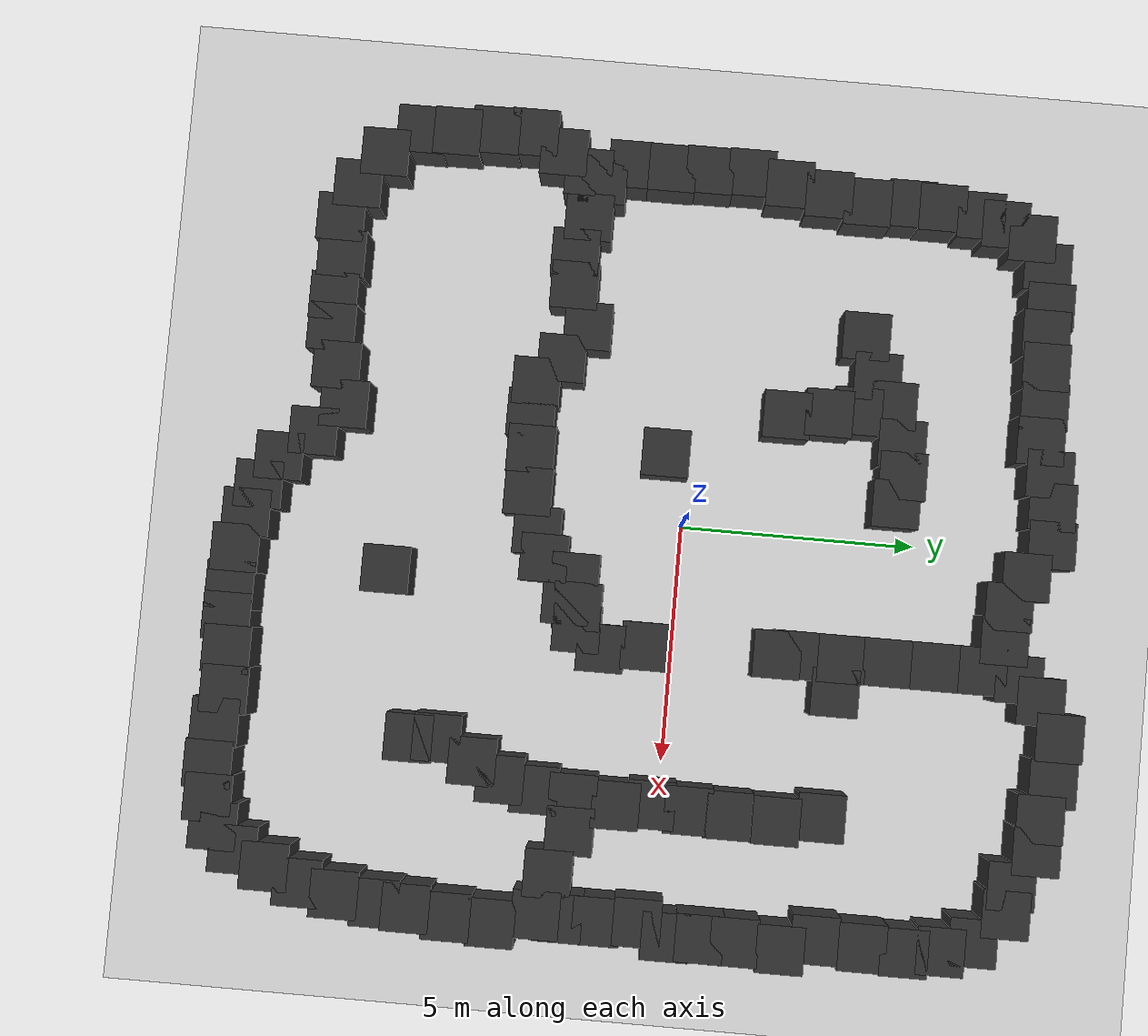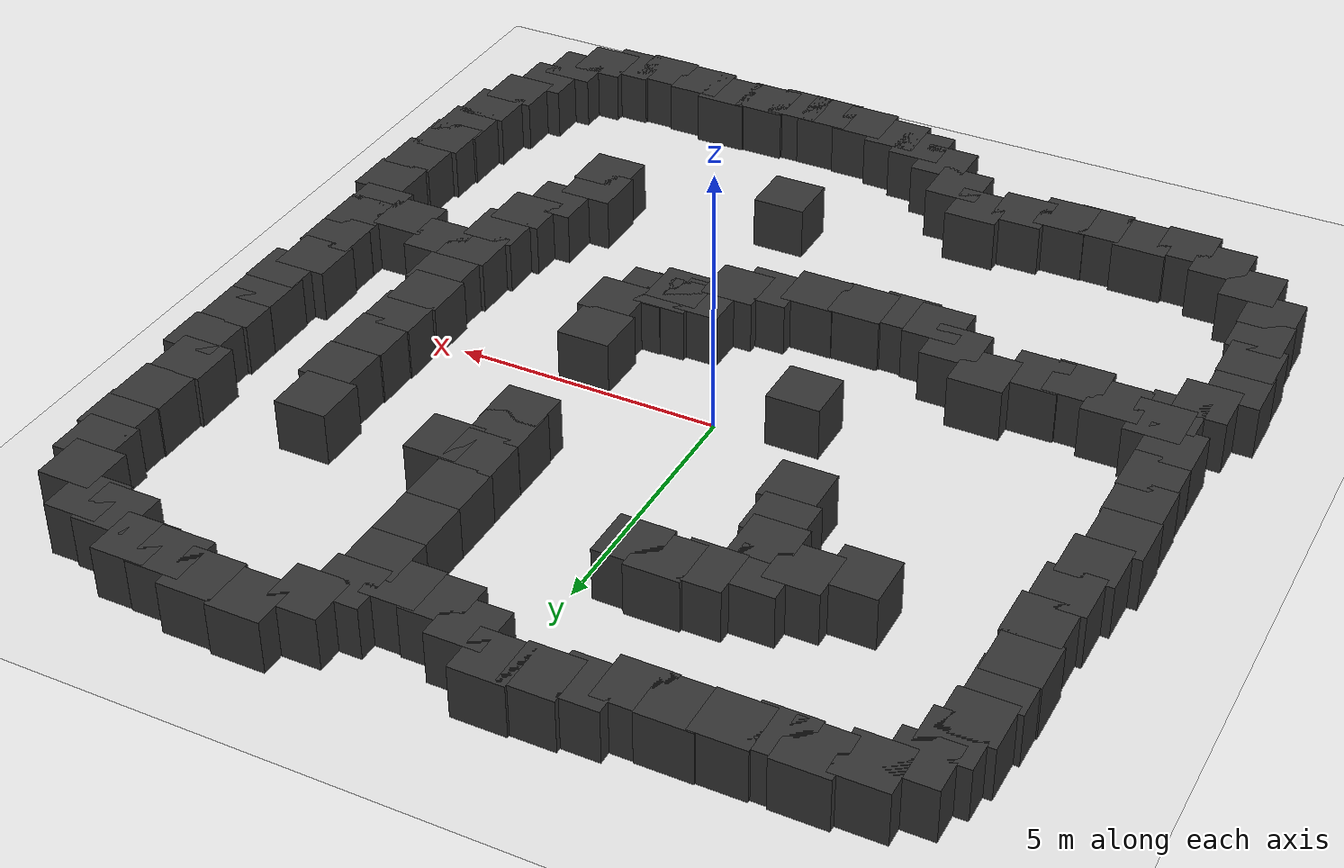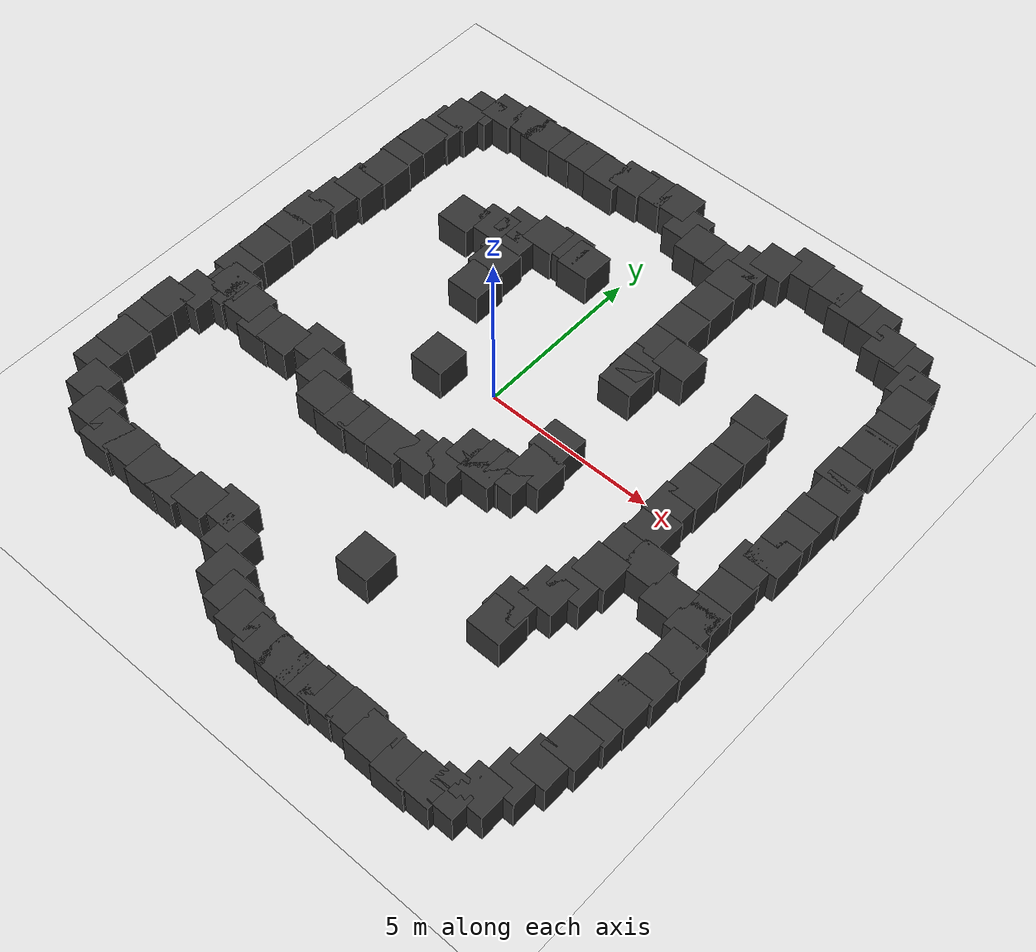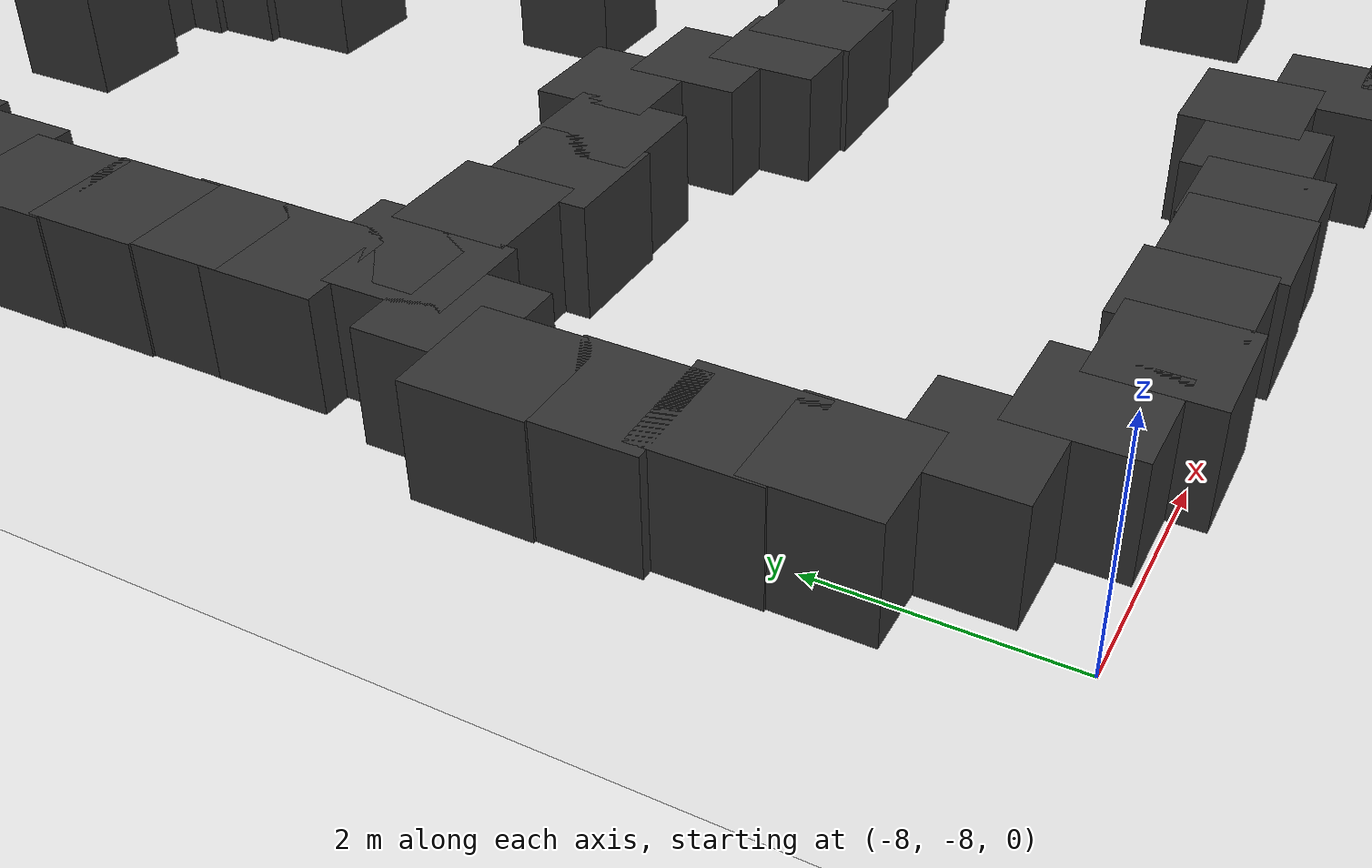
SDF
<?xml version="1.0"?>
<sdf version='1.10'>
  <world name='empty'>

    <physics name='1ms' type='ignored'>
      <max_step_size>0.001</max_step_size>
      <real_time_factor>1</real_time_factor>
      <real_time_update_rate>1000</real_time_update_rate>
    </physics>

    <plugin name='gz::sim::systems::Physics' filename='gz-sim-physics-system'/>
    <plugin name='gz::sim::systems::UserCommands' filename='gz-sim-user-commands-system'/>
    <plugin name='gz::sim::systems::SceneBroadcaster' filename='gz-sim-scene-broadcaster-system'/>
    <plugin name='gz::sim::systems::Contact' filename='gz-sim-contact-system'/>
    <gravity>0 0 -9.8000000000000007</gravity>
    <magnetic_field>5.5644999999999998e-06 2.2875799999999999e-05 -4.2388400000000002e-05</magnetic_field>
    <atmosphere type='adiabatic'/>

    <scene>
      <ambient>0.4 0.4 0.4 1</ambient>
      <background>0.7 0.7 0.7 1</background>
      <shadows>false</shadows>
    </scene>

    <model name='ground_plane'>
      <static>true</static>
      <link name='link'>
        <collision name='collision'>
          <geometry>
            <plane>
              <normal>0 0 1</normal>
              <size>100 100</size>
            </plane>
          </geometry>
          <surface>
            <friction>
              <ode/>
            </friction>
            <bounce/>
            <contact/>
          </surface>
        </collision>
        <visual name='visual'>
          <geometry>
            <plane>
              <normal>0 0 1</normal>
              <size>100 100</size>
            </plane>
          </geometry>
          <material>
            <ambient>0.9 0.9 0.9 1</ambient>
            <diffuse>0.9 0.9 0.9 1</diffuse>
            <specular>0.1 0.1 0.1 1</specular>
            <emissive>0.25 0.25 0.25 1</emissive>
          </material>
        </visual>
        <pose>0 0 0 0 0 0</pose>
        <inertial>
          <pose>0 0 0 0 0 0</pose>
          <mass>1</mass>
          <inertia>
            <ixx>1</ixx>
            <ixy>0</ixy>
            <ixz>0</ixz>
            <iyy>1</iyy>
            <iyz>0</iyz>
            <izz>1</izz>
          </inertia>
        </inertial>
        <enable_wind>false</enable_wind>
      </link>
      <pose>1 0 0 0 0 0</pose>
      <self_collide>false</self_collide>
    </model>

    <model name='box'>
      <pose>2.5 6.5 0.5 0 0 0</pose>
      <link name='box_link'>
        <inertial>
          <inertia>
            <ixx>0.16666</ixx>
            <ixy>0</ixy>
            <ixz>0</ixz>
            <iyy>0.16666</iyy>
            <iyz>0</iyz>
            <izz>0.16666</izz>
          </inertia>
          <mass>1</mass>
          <pose>0 0 0 0 0 0</pose>
        </inertial>
        <collision name='box_collision'>
          <geometry>
            <box>
              <size>1 1 1</size>
            </box>
          </geometry>
          <surface>
            <friction>
              <ode/>
            </friction>
            <bounce/>
            <contact/>
          </surface>
        </collision>
        <visual name='box_visual'>
          <geometry>
            <box>
              <size>1 1 1</size>
            </box>
          </geometry>
          <material>
            <ambient>0.1 0.1 0.1 1</ambient>
            <diffuse>0.2 0.2 0.2 1</diffuse>
            <specular>0.1 0.1 0.1 1</specular>
          </material>
        </visual>
        <pose>0 0 0 0 0 0</pose>
        <enable_wind>false</enable_wind>
      </link>
      <static>true</static>
      <self_collide>false</self_collide>
    </model>
    <model name='box_0'>
      <pose>2.5 5.5 0.5 0 0 0</pose>
      <link name='box_link'>
        <inertial>
          <inertia>
            <ixx>0.16666</ixx>
            <ixy>0</ixy>
            <ixz>0</ixz>
            <iyy>0.16666</iyy>
            <iyz>0</iyz>
            <izz>0.16666</izz>
          </inertia>
          <mass>1</mass>
          <pose>0 0 0 0 0 0</pose>
        </inertial>
        <collision name='box_collision'>
          <geometry>
            <box>
              <size>1 1 1</size>
            </box>
          </geometry>
          <surface>
            <friction>
              <ode/>
            </friction>
            <bounce/>
            <contact/>
          </surface>
        </collision>
        <visual name='box_visual'>
          <geometry>
            <box>
              <size>1 1 1</size>
            </box>
          </geometry>
          <material>
            <ambient>0.1 0.1 0.1 1</ambient>
            <diffuse>0.2 0.2 0.2 1</diffuse>
            <specular>0.1 0.1 0.1 1</specular>
          </material>
        </visual>
        <pose>0 0 0 0 0 0</pose>
        <enable_wind>false</enable_wind>
      </link>
      <static>true</static>
      <self_collide>false</self_collide>
    </model>
    <model name='box_1'>
      <pose>2.5 4.5 0.5 0 0 0</pose>
      <link name='box_link'>
        <inertial>
          <inertia>
            <ixx>0.16666</ixx>
            <ixy>0</ixy>
            <ixz>0</ixz>
            <iyy>0.16666</iyy>
            <iyz>0</iyz>
            <izz>0.16666</izz>
          </inertia>
          <mass>1</mass>
          <pose>0 0 0 0 0 0</pose>
        </inertial>
        <collision name='box_collision'>
          <geometry>
            <box>
              <size>1 1 1</size>
            </box>
          </geometry>
          <surface>
            <friction>
              <ode/>
            </friction>
            <bounce/>
            <contact/>
          </surface>
        </collision>
        <visual name='box_visual'>
          <geometry>
            <box>
              <size>1 1 1</size>
            </box>
          </geometry>
          <material>
            <ambient>0.1 0.1 0.1 1</ambient>
            <diffuse>0.2 0.2 0.2 1</diffuse>
            <specular>0.1 0.1 0.1 1</specular>
          </material>
        </visual>
        <pose>0 0 0 0 0 0</pose>
        <enable_wind>false</enable_wind>
      </link>
      <static>true</static>
      <self_collide>false</self_collide>
    </model>
    <model name='box_1_1'>
      <pose>2.5049385718494293 3.5486275147087847 0.5 0 0 0</pose>
      <link name='box_link'>
        <inertial>
          <inertia>
            <ixx>0.16666</ixx>
            <ixy>0</ixy>
            <ixz>0</ixz>
            <iyy>0.16666</iyy>
            <iyz>0</iyz>
            <izz>0.16666</izz>
          </inertia>
          <mass>1</mass>
        </inertial>
        <collision name='box_collision'>
          <geometry>
            <box>
              <size>1 1 1</size>
            </box>
          </geometry>
          <surface>
            <friction>
              <ode/>
            </friction>
            <bounce/>
            <contact/>
          </surface>
        </collision>
        <visual name='box_visual'>
          <geometry>
            <box>
              <size>1 1 1</size>
            </box>
          </geometry>
          <material>
            <ambient>0.1 0.1 0.1 1</ambient>
            <diffuse>0.2 0.2 0.2 1</diffuse>
            <specular>0.1 0.1 0.1 1</specular>
          </material>
        </visual>
      </link>
      <static>true</static>
      <self_collide>false</self_collide>
    </model>
    <model name='box_1_2'>
      <pose>2.5024154906887652 2.6663764751845518 0.5 0 0 0</pose>
      <link name='box_link'>
        <inertial>
          <inertia>
            <ixx>0.16666</ixx>
            <ixy>0</ixy>
            <ixz>0</ixz>
            <iyy>0.16666</iyy>
            <iyz>0</iyz>
            <izz>0.16666</izz>
          </inertia>
          <mass>1</mass>
        </inertial>
        <collision name='box_collision'>
          <geometry>
            <box>
              <size>1 1 1</size>
            </box>
          </geometry>
          <surface>
            <friction>
              <ode/>
            </friction>
            <bounce/>
            <contact/>
          </surface>
        </collision>
        <visual name='box_visual'>
          <geometry>
            <box>
              <size>1 1 1</size>
            </box>
          </geometry>
          <material>
            <ambient>0.1 0.1 0.1 1</ambient>
            <diffuse>0.2 0.2 0.2 1</diffuse>
            <specular>0.1 0.1 0.1 1</specular>
          </material>
        </visual>
      </link>
      <static>true</static>
      <self_collide>false</self_collide>
    </model>
    <model name='box_1_9'>
      <pose>1.2775530779215851 -2.1466495993404471 0.5 0 0 0</pose>
      <link name='box_link'>
        <inertial>
          <inertia>
            <ixx>0.16666</ixx>
            <ixy>0</ixy>
            <ixz>0</ixz>
            <iyy>0.16666</iyy>
            <iyz>0</iyz>
            <izz>0.16666</izz>
          </inertia>
          <mass>1</mass>
        </inertial>
        <collision name='box_collision'>
          <geometry>
            <box>
              <size>1 1 1</size>
            </box>
          </geometry>
          <surface>
            <friction>
              <ode/>
            </friction>
            <bounce/>
            <contact/>
          </surface>
        </collision>
        <visual name='box_visual'>
          <geometry>
            <box>
              <size>1 1 1</size>
            </box>
          </geometry>
          <material>
            <ambient>0.1 0.1 0.1 1</ambient>
            <diffuse>0.2 0.2 0.2 1</diffuse>
            <specular>0.1 0.1 0.1 1</specular>
          </material>
        </visual>
      </link>
      <static>true</static>
      <self_collide>false</self_collide>
    </model>
    <model name='box_1_10'>
      <pose>0.93467408876214897 -2.8259347033192812 0.5 0 0 0</pose>
      <link name='box_link'>
        <inertial>
          <inertia>
            <ixx>0.16666</ixx>
            <ixy>0</ixy>
            <ixz>0</ixz>
            <iyy>0.16666</iyy>
            <iyz>0</iyz>
            <izz>0.16666</izz>
          </inertia>
          <mass>1</mass>
        </inertial>
        <collision name='box_collision'>
          <geometry>
            <box>
              <size>1 1 1</size>
            </box>
          </geometry>
          <surface>
            <friction>
              <ode/>
            </friction>
            <bounce/>
            <contact/>
          </surface>
        </collision>
        <visual name='box_visual'>
          <geometry>
            <box>
              <size>1 1 1</size>
            </box>
          </geometry>
          <material>
            <ambient>0.1 0.1 0.1 1</ambient>
            <diffuse>0.2 0.2 0.2 1</diffuse>
            <specular>0.1 0.1 0.1 1</specular>
          </material>
        </visual>
      </link>
      <static>true</static>
      <self_collide>false</self_collide>
    </model>
    <model name='box_1_11'>
      <pose>0.37469805444032767 -3.0175223676698071 0.5 0 0 0</pose>
      <link name='box_link'>
        <inertial>
          <inertia>
            <ixx>0.16666</ixx>
            <ixy>0</ixy>
            <ixz>0</ixz>
            <iyy>0.16666</iyy>
            <iyz>0</iyz>
            <izz>0.16666</izz>
          </inertia>
          <mass>1</mass>
        </inertial>
        <collision name='box_collision'>
          <geometry>
            <box>
              <size>1 1 1</size>
            </box>
          </geometry>
          <surface>
            <friction>
              <ode/>
            </friction>
            <bounce/>
            <contact/>
          </surface>
        </collision>
        <visual name='box_visual'>
          <geometry>
            <box>
              <size>1 1 1</size>
            </box>
          </geometry>
          <material>
            <ambient>0.1 0.1 0.1 1</ambient>
            <diffuse>0.2 0.2 0.2 1</diffuse>
            <specular>0.1 0.1 0.1 1</specular>
          </material>
        </visual>
      </link>
      <static>true</static>
      <self_collide>false</self_collide>
    </model>
    <model name='box_1_12'>
      <pose>-0.42770161789153849 -3.2795379376203195 0.5 0 0 0</pose>
      <link name='box_link'>
        <inertial>
          <inertia>
            <ixx>0.16666</ixx>
            <ixy>0</ixy>
            <ixz>0</ixz>
            <iyy>0.16666</iyy>
            <iyz>0</iyz>
            <izz>0.16666</izz>
          </inertia>
          <mass>1</mass>
        </inertial>
        <collision name='box_collision'>
          <geometry>
            <box>
              <size>1 1 1</size>
            </box>
          </geometry>
          <surface>
            <friction>
              <ode/>
            </friction>
            <bounce/>
            <contact/>
          </surface>
        </collision>
        <visual name='box_visual'>
          <geometry>
            <box>
              <size>1 1 1</size>
            </box>
          </geometry>
          <material>
            <ambient>0.1 0.1 0.1 1</ambient>
            <diffuse>0.2 0.2 0.2 1</diffuse>
            <specular>0.1 0.1 0.1 1</specular>
          </material>
        </visual>
      </link>
      <static>true</static>
      <self_collide>false</self_collide>
    </model>
    <model name='box_1_13'>
      <pose>-1.3258233026676089 -3.2989898374171354 0.5 0 0 0</pose>
      <link name='box_link'>
        <inertial>
          <inertia>
            <ixx>0.16666</ixx>
            <ixy>0</ixy>
            <ixz>0</ixz>
            <iyy>0.16666</iyy>
            <iyz>0</iyz>
            <izz>0.16666</izz>
          </inertia>
          <mass>1</mass>
        </inertial>
        <collision name='box_collision'>
          <geometry>
            <box>
              <size>1 1 1</size>
            </box>
          </geometry>
          <surface>
            <friction>
              <ode/>
            </friction>
            <bounce/>
            <contact/>
          </surface>
        </collision>
        <visual name='box_visual'>
          <geometry>
            <box>
              <size>1 1 1</size>
            </box>
          </geometry>
          <material>
            <ambient>0.1 0.1 0.1 1</ambient>
            <diffuse>0.2 0.2 0.2 1</diffuse>
            <specular>0.1 0.1 0.1 1</specular>
          </material>
        </visual>
      </link>
      <static>true</static>
      <self_collide>false</self_collide>
    </model>
    <model name='box_1_14'>
      <pose>-2.0768754887676213 -3.3662396268547674 0.5 0 0 0</pose>
      <link name='box_link'>
        <inertial>
          <inertia>
            <ixx>0.16666</ixx>
            <ixy>0</ixy>
            <ixz>0</ixz>
            <iyy>0.16666</iyy>
            <iyz>0</iyz>
            <izz>0.16666</izz>
          </inertia>
          <mass>1</mass>
        </inertial>
        <collision name='box_collision'>
          <geometry>
            <box>
              <size>1 1 1</size>
            </box>
          </geometry>
          <surface>
            <friction>
              <ode/>
            </friction>
            <bounce/>
            <contact/>
          </surface>
        </collision>
        <visual name='box_visual'>
          <geometry>
            <box>
              <size>1 1 1</size>
            </box>
          </geometry>
          <material>
            <ambient>0.1 0.1 0.1 1</ambient>
            <diffuse>0.2 0.2 0.2 1</diffuse>
            <specular>0.1 0.1 0.1 1</specular>
          </material>
        </visual>
      </link>
      <static>true</static>
      <self_collide>false</self_collide>
    </model>
    <model name='box_1_15'>
      <pose>-2.7543442581268471 -3.3133205585828689 0.5 0 0 0</pose>
      <link name='box_link'>
        <inertial>
          <inertia>
            <ixx>0.16666</ixx>
            <ixy>0</ixy>
            <ixz>0</ixz>
            <iyy>0.16666</iyy>
            <iyz>0</iyz>
            <izz>0.16666</izz>
          </inertia>
          <mass>1</mass>
        </inertial>
        <collision name='box_collision'>
          <geometry>
            <box>
              <size>1 1 1</size>
            </box>
          </geometry>
          <surface>
            <friction>
              <ode/>
            </friction>
            <bounce/>
            <contact/>
          </surface>
        </collision>
        <visual name='box_visual'>
          <geometry>
            <box>
              <size>1 1 1</size>
            </box>
          </geometry>
          <material>
            <ambient>0.1 0.1 0.1 1</ambient>
            <diffuse>0.2 0.2 0.2 1</diffuse>
            <specular>0.1 0.1 0.1 1</specular>
          </material>
        </visual>
      </link>
      <static>true</static>
      <self_collide>false</self_collide>
    </model>
    <model name='box_1_16'>
      <pose>-3.2850646331188065 -2.8248588929853842 0.5 0 0 0</pose>
      <link name='box_link'>
        <inertial>
          <inertia>
            <ixx>0.16666</ixx>
            <ixy>0</ixy>
            <ixz>0</ixz>
            <iyy>0.16666</iyy>
            <iyz>0</iyz>
            <izz>0.16666</izz>
          </inertia>
          <mass>1</mass>
        </inertial>
        <collision name='box_collision'>
          <geometry>
            <box>
              <size>1 1 1</size>
            </box>
          </geometry>
          <surface>
            <friction>
              <ode/>
            </friction>
            <bounce/>
            <contact/>
          </surface>
        </collision>
        <visual name='box_visual'>
          <geometry>
            <box>
              <size>1 1 1</size>
            </box>
          </geometry>
          <material>
            <ambient>0.1 0.1 0.1 1</ambient>
            <diffuse>0.2 0.2 0.2 1</diffuse>
            <specular>0.1 0.1 0.1 1</specular>
          </material>
        </visual>
      </link>
      <static>true</static>
      <self_collide>false</self_collide>
    </model>
    <model name='box_1_17'>
      <pose>-4.0074305669833405 -2.3352447081539247 0.5 0 0 0</pose>
      <link name='box_link'>
        <inertial>
          <inertia>
            <ixx>0.16666</ixx>
            <ixy>0</ixy>
            <ixz>0</ixz>
            <iyy>0.16666</iyy>
            <iyz>0</iyz>
            <izz>0.16666</izz>
          </inertia>
          <mass>1</mass>
        </inertial>
        <collision name='box_collision'>
          <geometry>
            <box>
              <size>1 1 1</size>
            </box>
          </geometry>
          <surface>
            <friction>
              <ode/>
            </friction>
            <bounce/>
            <contact/>
          </surface>
        </collision>
        <visual name='box_visual'>
          <geometry>
            <box>
              <size>1 1 1</size>
            </box>
          </geometry>
          <material>
            <ambient>0.1 0.1 0.1 1</ambient>
            <diffuse>0.2 0.2 0.2 1</diffuse>
            <specular>0.1 0.1 0.1 1</specular>
          </material>
        </visual>
      </link>
      <static>true</static>
      <self_collide>false</self_collide>
    </model>
    <model name='box_1_18'>
      <pose>-4.8523228903674607 -2.6936452917574178 0.5 0 0 0</pose>
      <link name='box_link'>
        <inertial>
          <inertia>
            <ixx>0.16666</ixx>
            <ixy>0</ixy>
            <ixz>0</ixz>
            <iyy>0.16666</iyy>
            <iyz>0</iyz>
            <izz>0.16666</izz>
          </inertia>
          <mass>1</mass>
        </inertial>
        <collision name='box_collision'>
          <geometry>
            <box>
              <size>1 1 1</size>
            </box>
          </geometry>
          <surface>
            <friction>
              <ode/>
            </friction>
            <bounce/>
            <contact/>
          </surface>
        </collision>
        <visual name='box_visual'>
          <geometry>
            <box>
              <size>1 1 1</size>
            </box>
          </geometry>
          <material>
            <ambient>0.1 0.1 0.1 1</ambient>
            <diffuse>0.2 0.2 0.2 1</diffuse>
            <specular>0.1 0.1 0.1 1</specular>
          </material>
        </visual>
      </link>
      <static>true</static>
      <self_collide>false</self_collide>
    </model>
    <model name='box_1_19'>
      <pose>-5.5509077407547895 -2.7376141223321713 0.5 0 0 0</pose>
      <link name='box_link'>
        <inertial>
          <inertia>
            <ixx>0.16666</ixx>
            <ixy>0</ixy>
            <ixz>0</ixz>
            <iyy>0.16666</iyy>
            <iyz>0</iyz>
            <izz>0.16666</izz>
          </inertia>
          <mass>1</mass>
        </inertial>
        <collision name='box_collision'>
          <geometry>
            <box>
              <size>1 1 1</size>
            </box>
          </geometry>
          <surface>
            <friction>
              <ode/>
            </friction>
            <bounce/>
            <contact/>
          </surface>
        </collision>
        <visual name='box_visual'>
          <geometry>
            <box>
              <size>1 1 1</size>
            </box>
          </geometry>
          <material>
            <ambient>0.1 0.1 0.1 1</ambient>
            <diffuse>0.2 0.2 0.2 1</diffuse>
            <specular>0.1 0.1 0.1 1</specular>
          </material>
        </visual>
      </link>
      <static>true</static>
      <self_collide>false</self_collide>
    </model>
    <model name='box_1_20'>
      <pose>-6.3205569848411018 -2.5159512534173127 0.5 0 0 0</pose>
      <link name='box_link'>
        <inertial>
          <inertia>
            <ixx>0.16666</ixx>
            <ixy>0</ixy>
            <ixz>0</ixz>
            <iyy>0.16666</iyy>
            <iyz>0</iyz>
            <izz>0.16666</izz>
          </inertia>
          <mass>1</mass>
        </inertial>
        <collision name='box_collision'>
          <geometry>
            <box>
              <size>1 1 1</size>
            </box>
          </geometry>
          <surface>
            <friction>
              <ode/>
            </friction>
            <bounce/>
            <contact/>
          </surface>
        </collision>
        <visual name='box_visual'>
          <geometry>
            <box>
              <size>1 1 1</size>
            </box>
          </geometry>
          <material>
            <ambient>0.1 0.1 0.1 1</ambient>
            <diffuse>0.2 0.2 0.2 1</diffuse>
            <specular>0.1 0.1 0.1 1</specular>
          </material>
        </visual>
      </link>
      <static>true</static>
      <self_collide>false</self_collide>
    </model>
    <model name='box_1_21'>
      <pose>-7.1347157242386761 -2.2923898937746197 0.5 0 0 0</pose>
      <link name='box_link'>
        <inertial>
          <inertia>
            <ixx>0.16666</ixx>
            <ixy>0</ixy>
            <ixz>0</ixz>
            <iyy>0.16666</iyy>
            <iyz>0</iyz>
            <izz>0.16666</izz>
          </inertia>
          <mass>1</mass>
        </inertial>
        <collision name='box_collision'>
          <geometry>
            <box>
              <size>1 1 1</size>
            </box>
          </geometry>
          <surface>
            <friction>
              <ode/>
            </friction>
            <bounce/>
            <contact/>
          </surface>
        </collision>
        <visual name='box_visual'>
          <geometry>
            <box>
              <size>1 1 1</size>
            </box>
          </geometry>
          <material>
            <ambient>0.1 0.1 0.1 1</ambient>
            <diffuse>0.2 0.2 0.2 1</diffuse>
            <specular>0.1 0.1 0.1 1</specular>
          </material>
        </visual>
      </link>
      <static>true</static>
      <self_collide>false</self_collide>
    </model>
    <model name='box_1_22'>
      <pose>1.8390095776884428 6.9125247101005636 0.5 0 0 0</pose>
      <link name='box_link'>
        <inertial>
          <inertia>
            <ixx>0.16666</ixx>
            <ixy>0</ixy>
            <ixz>0</ixz>
            <iyy>0.16666</iyy>
            <iyz>0</iyz>
            <izz>0.16666</izz>
          </inertia>
          <mass>1</mass>
        </inertial>
        <collision name='box_collision'>
          <geometry>
            <box>
              <size>1 1 1</size>
            </box>
          </geometry>
          <surface>
            <friction>
              <ode/>
            </friction>
            <bounce/>
            <contact/>
          </surface>
        </collision>
        <visual name='box_visual'>
          <geometry>
            <box>
              <size>1 1 1</size>
            </box>
          </geometry>
          <material>
            <ambient>0.1 0.1 0.1 1</ambient>
            <diffuse>0.2 0.2 0.2 1</diffuse>
            <specular>0.1 0.1 0.1 1</specular>
          </material>
        </visual>
      </link>
      <static>true</static>
      <self_collide>false</self_collide>
    </model>
    <model name='box_2'>
      <pose>2.5953931885466908 -0.55783518179751967 0.5 0 0 0</pose>
      <link name='box_link'>
        <inertial>
          <inertia>
            <ixx>0.16666</ixx>
            <ixy>0</ixy>
            <ixz>0</ixz>
            <iyy>0.16666</iyy>
            <iyz>0</iyz>
            <izz>0.16666</izz>
          </inertia>
          <mass>1</mass>
          <pose>0 0 0 0 0 0</pose>
        </inertial>
        <collision name='box_collision'>
          <geometry>
            <box>
              <size>1 1 1</size>
            </box>
          </geometry>
          <surface>
            <friction>
              <ode/>
            </friction>
            <bounce/>
            <contact/>
          </surface>
        </collision>
        <visual name='box_visual'>
          <geometry>
            <box>
              <size>1 1 1</size>
            </box>
          </geometry>
          <material>
            <ambient>0.1 0.1 0.1 1</ambient>
            <diffuse>0.2 0.2 0.2 1</diffuse>
            <specular>0.1 0.1 0.1 1</specular>
          </material>
        </visual>
        <pose>0 0 0 0 0 0</pose>
        <enable_wind>false</enable_wind>
      </link>
      <static>true</static>
      <self_collide>false</self_collide>
    </model>
    <model name='box_1_6'>
      <pose>2.7144813404287431 -1.4841461804021554 0.5 0 0 0</pose>
      <link name='box_link'>
        <inertial>
          <inertia>
            <ixx>0.16666</ixx>
            <ixy>0</ixy>
            <ixz>0</ixz>
            <iyy>0.16666</iyy>
            <iyz>0</iyz>
            <izz>0.16666</izz>
          </inertia>
          <mass>1</mass>
        </inertial>
        <collision name='box_collision'>
          <geometry>
            <box>
              <size>1 1 1</size>
            </box>
          </geometry>
          <surface>
            <friction>
              <ode/>
            </friction>
            <bounce/>
            <contact/>
          </surface>
        </collision>
        <visual name='box_visual'>
          <geometry>
            <box>
              <size>1 1 1</size>
            </box>
          </geometry>
          <material>
            <ambient>0.1 0.1 0.1 1</ambient>
            <diffuse>0.2 0.2 0.2 1</diffuse>
            <specular>0.1 0.1 0.1 1</specular>
          </material>
        </visual>
      </link>
      <static>true</static>
      <self_collide>false</self_collide>
    </model>
    <model name='box_1_7'>
      <pose>2.3474095850875694 -2.0197217037473632 0.5 0 0 0</pose>
      <link name='box_link'>
        <inertial>
          <inertia>
            <ixx>0.16666</ixx>
            <ixy>0</ixy>
            <ixz>0</ixz>
            <iyy>0.16666</iyy>
            <iyz>0</iyz>
            <izz>0.16666</izz>
          </inertia>
          <mass>1</mass>
        </inertial>
        <collision name='box_collision'>
          <geometry>
            <box>
              <size>1 1 1</size>
            </box>
          </geometry>
          <surface>
            <friction>
              <ode/>
            </friction>
            <bounce/>
            <contact/>
          </surface>
        </collision>
        <visual name='box_visual'>
          <geometry>
            <box>
              <size>1 1 1</size>
            </box>
          </geometry>
          <material>
            <ambient>0.1 0.1 0.1 1</ambient>
            <diffuse>0.2 0.2 0.2 1</diffuse>
            <specular>0.1 0.1 0.1 1</specular>
          </material>
        </visual>
      </link>
      <static>true</static>
      <self_collide>false</self_collide>
    </model>
    <model name='box_1_8'>
      <pose>1.7857908999247307 -2.2853107042336149 0.5 0 0 0</pose>
      <link name='box_link'>
        <inertial>
          <inertia>
            <ixx>0.16666</ixx>
            <ixy>0</ixy>
            <ixz>0</ixz>
            <iyy>0.16666</iyy>
            <iyz>0</iyz>
            <izz>0.16666</izz>
          </inertia>
          <mass>1</mass>
        </inertial>
        <collision name='box_collision'>
          <geometry>
            <box>
              <size>1 1 1</size>
            </box>
          </geometry>
          <surface>
            <friction>
              <ode/>
            </friction>
            <bounce/>
            <contact/>
          </surface>
        </collision>
        <visual name='box_visual'>
          <geometry>
            <box>
              <size>1 1 1</size>
            </box>
          </geometry>
          <material>
            <ambient>0.1 0.1 0.1 1</ambient>
            <diffuse>0.2 0.2 0.2 1</diffuse>
            <specular>0.1 0.1 0.1 1</specular>
          </material>
        </visual>
      </link>
      <static>true</static>
      <self_collide>false</self_collide>
    </model>
    <model name='box_1_23'>
      <pose>1.8839879778759476 -2.042191215790619 0.5 0 0 0</pose>
      <link name='box_link'>
        <inertial>
          <inertia>
            <ixx>0.16666</ixx>
            <ixy>0</ixy>
            <ixz>0</ixz>
            <iyy>0.16666</iyy>
            <iyz>0</iyz>
            <izz>0.16666</izz>
          </inertia>
          <mass>1</mass>
        </inertial>
        <collision name='box_collision'>
          <geometry>
            <box>
              <size>1 1 1</size>
            </box>
          </geometry>
          <surface>
            <friction>
              <ode/>
            </friction>
            <bounce/>
            <contact/>
          </surface>
        </collision>
        <visual name='box_visual'>
          <geometry>
            <box>
              <size>1 1 1</size>
            </box>
          </geometry>
          <material>
            <ambient>0.1 0.1 0.1 1</ambient>
            <diffuse>0.2 0.2 0.2 1</diffuse>
            <specular>0.1 0.1 0.1 1</specular>
          </material>
        </visual>
      </link>
      <static>true</static>
      <self_collide>false</self_collide>
    </model>
    <model name='box_1_24'>
      <pose>1.1212766443522475 6.951842859925919 0.5 0 0 0</pose>
      <link name='box_link'>
        <inertial>
          <inertia>
            <ixx>0.16666</ixx>
            <ixy>0</ixy>
            <ixz>0</ixz>
            <iyy>0.16666</iyy>
            <iyz>0</iyz>
            <izz>0.16666</izz>
          </inertia>
          <mass>1</mass>
        </inertial>
        <collision name='box_collision'>
          <geometry>
            <box>
              <size>1 1 1</size>
            </box>
          </geometry>
          <surface>
            <friction>
              <ode/>
            </friction>
            <bounce/>
            <contact/>
          </surface>
        </collision>
        <visual name='box_visual'>
          <geometry>
            <box>
              <size>1 1 1</size>
            </box>
          </geometry>
          <material>
            <ambient>0.1 0.1 0.1 1</ambient>
            <diffuse>0.2 0.2 0.2 1</diffuse>
            <specular>0.1 0.1 0.1 1</specular>
          </material>
        </visual>
      </link>
      <static>true</static>
      <self_collide>false</self_collide>
    </model>
    <model name='box_1_25'>
      <pose>0.46318117788749635 7.2653021997369533 0.5 0 0 0</pose>
      <link name='box_link'>
        <inertial>
          <inertia>
            <ixx>0.16666</ixx>
            <ixy>0</ixy>
            <ixz>0</ixz>
            <iyy>0.16666</iyy>
            <iyz>0</iyz>
            <izz>0.16666</izz>
          </inertia>
          <mass>1</mass>
        </inertial>
        <collision name='box_collision'>
          <geometry>
            <box>
              <size>1 1 1</size>
            </box>
          </geometry>
          <surface>
            <friction>
              <ode/>
            </friction>
            <bounce/>
            <contact/>
          </surface>
        </collision>
        <visual name='box_visual'>
          <geometry>
            <box>
              <size>1 1 1</size>
            </box>
          </geometry>
          <material>
            <ambient>0.1 0.1 0.1 1</ambient>
            <diffuse>0.2 0.2 0.2 1</diffuse>
            <specular>0.1 0.1 0.1 1</specular>
          </material>
        </visual>
      </link>
      <static>true</static>
      <self_collide>false</self_collide>
    </model>
    <model name='box_1_26'>
      <pose>-0.24174810026960936 7.7513211208967068 0.5 0 0 0</pose>
      <link name='box_link'>
        <inertial>
          <inertia>
            <ixx>0.16666</ixx>
            <ixy>0</ixy>
            <ixz>0</ixz>
            <iyy>0.16666</iyy>
            <iyz>0</iyz>
            <izz>0.16666</izz>
          </inertia>
          <mass>1</mass>
        </inertial>
        <collision name='box_collision'>
          <geometry>
            <box>
              <size>1 1 1</size>
            </box>
          </geometry>
          <surface>
            <friction>
              <ode/>
            </friction>
            <bounce/>
            <contact/>
          </surface>
        </collision>
        <visual name='box_visual'>
          <geometry>
            <box>
              <size>1 1 1</size>
            </box>
          </geometry>
          <material>
            <ambient>0.1 0.1 0.1 1</ambient>
            <diffuse>0.2 0.2 0.2 1</diffuse>
            <specular>0.1 0.1 0.1 1</specular>
          </material>
        </visual>
      </link>
      <static>true</static>
      <self_collide>false</self_collide>
    </model>
    <model name='box_1_27'>
      <pose>-1.0430317366710962 7.6998609396056308 0.5 0 0 0</pose>
      <link name='box_link'>
        <inertial>
          <inertia>
            <ixx>0.16666</ixx>
            <ixy>0</ixy>
            <ixz>0</ixz>
            <iyy>0.16666</iyy>
            <iyz>0</iyz>
            <izz>0.16666</izz>
          </inertia>
          <mass>1</mass>
        </inertial>
        <collision name='box_collision'>
          <geometry>
            <box>
              <size>1 1 1</size>
            </box>
          </geometry>
          <surface>
            <friction>
              <ode/>
            </friction>
            <bounce/>
            <contact/>
          </surface>
        </collision>
        <visual name='box_visual'>
          <geometry>
            <box>
              <size>1 1 1</size>
            </box>
          </geometry>
          <material>
            <ambient>0.1 0.1 0.1 1</ambient>
            <diffuse>0.2 0.2 0.2 1</diffuse>
            <specular>0.1 0.1 0.1 1</specular>
          </material>
        </visual>
      </link>
      <static>true</static>
      <self_collide>false</self_collide>
    </model>
    <model name='box_1_28'>
      <pose>-1.7239461451952849 7.5983014230268555 0.5 0 0 0</pose>
      <link name='box_link'>
        <inertial>
          <inertia>
            <ixx>0.16666</ixx>
            <ixy>0</ixy>
            <ixz>0</ixz>
            <iyy>0.16666</iyy>
            <iyz>0</iyz>
            <izz>0.16666</izz>
          </inertia>
          <mass>1</mass>
        </inertial>
        <collision name='box_collision'>
          <geometry>
            <box>
              <size>1 1 1</size>
            </box>
          </geometry>
          <surface>
            <friction>
              <ode/>
            </friction>
            <bounce/>
            <contact/>
          </surface>
        </collision>
        <visual name='box_visual'>
          <geometry>
            <box>
              <size>1 1 1</size>
            </box>
          </geometry>
          <material>
            <ambient>0.1 0.1 0.1 1</ambient>
            <diffuse>0.2 0.2 0.2 1</diffuse>
            <specular>0.1 0.1 0.1 1</specular>
          </material>
        </visual>
      </link>
      <static>true</static>
      <self_collide>false</self_collide>
    </model>
    <model name='box_1_29'>
      <pose>-2.4038024197089833 7.3552581151350873 0.5 0 0 0</pose>
      <link name='box_link'>
        <inertial>
          <inertia>
            <ixx>0.16666</ixx>
            <ixy>0</ixy>
            <ixz>0</ixz>
            <iyy>0.16666</iyy>
            <iyz>0</iyz>
            <izz>0.16666</izz>
          </inertia>
          <mass>1</mass>
        </inertial>
        <collision name='box_collision'>
          <geometry>
            <box>
              <size>1 1 1</size>
            </box>
          </geometry>
          <surface>
            <friction>
              <ode/>
            </friction>
            <bounce/>
            <contact/>
          </surface>
        </collision>
        <visual name='box_visual'>
          <geometry>
            <box>
              <size>1 1 1</size>
            </box>
          </geometry>
          <material>
            <ambient>0.1 0.1 0.1 1</ambient>
            <diffuse>0.2 0.2 0.2 1</diffuse>
            <specular>0.1 0.1 0.1 1</specular>
          </material>
        </visual>
      </link>
      <static>true</static>
      <self_collide>false</self_collide>
    </model>
    <model name='box_1_30'>
      <pose>-3.1305321310097356 7.3768259517108445 0.5 0 0 0</pose>
      <link name='box_link'>
        <inertial>
          <inertia>
            <ixx>0.16666</ixx>
            <ixy>0</ixy>
            <ixz>0</ixz>
            <iyy>0.16666</iyy>
            <iyz>0</iyz>
            <izz>0.16666</izz>
          </inertia>
          <mass>1</mass>
        </inertial>
        <collision name='box_collision'>
          <geometry>
            <box>
              <size>1 1 1</size>
            </box>
          </geometry>
          <surface>
            <friction>
              <ode/>
            </friction>
            <bounce/>
            <contact/>
          </surface>
        </collision>
        <visual name='box_visual'>
          <geometry>
            <box>
              <size>1 1 1</size>
            </box>
          </geometry>
          <material>
            <ambient>0.1 0.1 0.1 1</ambient>
            <diffuse>0.2 0.2 0.2 1</diffuse>
            <specular>0.1 0.1 0.1 1</specular>
          </material>
        </visual>
      </link>
      <static>true</static>
      <self_collide>false</self_collide>
    </model>
    <model name='box_1_31'>
      <pose>-3.9780258645429649 7.3516122676149367 0.5 0 0 0</pose>
      <link name='box_link'>
        <inertial>
          <inertia>
            <ixx>0.16666</ixx>
            <ixy>0</ixy>
            <ixz>0</ixz>
            <iyy>0.16666</iyy>
            <iyz>0</iyz>
            <izz>0.16666</izz>
          </inertia>
          <mass>1</mass>
        </inertial>
        <collision name='box_collision'>
          <geometry>
            <box>
              <size>1 1 1</size>
            </box>
          </geometry>
          <surface>
            <friction>
              <ode/>
            </friction>
            <bounce/>
            <contact/>
          </surface>
        </collision>
        <visual name='box_visual'>
          <geometry>
            <box>
              <size>1 1 1</size>
            </box>
          </geometry>
          <material>
            <ambient>0.1 0.1 0.1 1</ambient>
            <diffuse>0.2 0.2 0.2 1</diffuse>
            <specular>0.1 0.1 0.1 1</specular>
          </material>
        </visual>
      </link>
      <static>true</static>
      <self_collide>false</self_collide>
    </model>
    <model name='box_1_32'>
      <pose>-4.6791211502954528 7.30150294179818 0.5 0 0 0</pose>
      <link name='box_link'>
        <inertial>
          <inertia>
            <ixx>0.16666</ixx>
            <ixy>0</ixy>
            <ixz>0</ixz>
            <iyy>0.16666</iyy>
            <iyz>0</iyz>
            <izz>0.16666</izz>
          </inertia>
          <mass>1</mass>
        </inertial>
        <collision name='box_collision'>
          <geometry>
            <box>
              <size>1 1 1</size>
            </box>
          </geometry>
          <surface>
            <friction>
              <ode/>
            </friction>
            <bounce/>
            <contact/>
          </surface>
        </collision>
        <visual name='box_visual'>
          <geometry>
            <box>
              <size>1 1 1</size>
            </box>
          </geometry>
          <material>
            <ambient>0.1 0.1 0.1 1</ambient>
            <diffuse>0.2 0.2 0.2 1</diffuse>
            <specular>0.1 0.1 0.1 1</specular>
          </material>
        </visual>
      </link>
      <static>true</static>
      <self_collide>false</self_collide>
    </model>
    <model name='box_1_33'>
      <pose>-5.2585458140984302 7.3480616508151568 0.5 0 0 0</pose>
      <link name='box_link'>
        <inertial>
          <inertia>
            <ixx>0.16666</ixx>
            <ixy>0</ixy>
            <ixz>0</ixz>
            <iyy>0.16666</iyy>
            <iyz>0</iyz>
            <izz>0.16666</izz>
          </inertia>
          <mass>1</mass>
        </inertial>
        <collision name='box_collision'>
          <geometry>
            <box>
              <size>1 1 1</size>
            </box>
          </geometry>
          <surface>
            <friction>
              <ode/>
            </friction>
            <bounce/>
            <contact/>
          </surface>
        </collision>
        <visual name='box_visual'>
          <geometry>
            <box>
              <size>1 1 1</size>
            </box>
          </geometry>
          <material>
            <ambient>0.1 0.1 0.1 1</ambient>
            <diffuse>0.2 0.2 0.2 1</diffuse>
            <specular>0.1 0.1 0.1 1</specular>
          </material>
        </visual>
      </link>
      <static>true</static>
      <self_collide>false</self_collide>
    </model>
    <model name='box_1_34'>
      <pose>-6.1023071177948891 7.2247757718515402 0.5 0 0 0</pose>
      <link name='box_link'>
        <inertial>
          <inertia>
            <ixx>0.16666</ixx>
            <ixy>0</ixy>
            <ixz>0</ixz>
            <iyy>0.16666</iyy>
            <iyz>0</iyz>
            <izz>0.16666</izz>
          </inertia>
          <mass>1</mass>
        </inertial>
        <collision name='box_collision'>
          <geometry>
            <box>
              <size>1 1 1</size>
            </box>
          </geometry>
          <surface>
            <friction>
              <ode/>
            </friction>
            <bounce/>
            <contact/>
          </surface>
        </collision>
        <visual name='box_visual'>
          <geometry>
            <box>
              <size>1 1 1</size>
            </box>
          </geometry>
          <material>
            <ambient>0.1 0.1 0.1 1</ambient>
            <diffuse>0.2 0.2 0.2 1</diffuse>
            <specular>0.1 0.1 0.1 1</specular>
          </material>
        </visual>
      </link>
      <static>true</static>
      <self_collide>false</self_collide>
    </model>
    <model name='box_1_35'>
      <pose>-6.6819798126192902 6.8613695117720566 0.5 0 0 0</pose>
      <link name='box_link'>
        <inertial>
          <inertia>
            <ixx>0.16666</ixx>
            <ixy>0</ixy>
            <ixz>0</ixz>
            <iyy>0.16666</iyy>
            <iyz>0</iyz>
            <izz>0.16666</izz>
          </inertia>
          <mass>1</mass>
        </inertial>
        <collision name='box_collision'>
          <geometry>
            <box>
              <size>1 1 1</size>
            </box>
          </geometry>
          <surface>
            <friction>
              <ode/>
            </friction>
            <bounce/>
            <contact/>
          </surface>
        </collision>
        <visual name='box_visual'>
          <geometry>
            <box>
              <size>1 1 1</size>
            </box>
          </geometry>
          <material>
            <ambient>0.1 0.1 0.1 1</ambient>
            <diffuse>0.2 0.2 0.2 1</diffuse>
            <specular>0.1 0.1 0.1 1</specular>
          </material>
        </visual>
      </link>
      <static>true</static>
      <self_collide>false</self_collide>
    </model>
    <model name='box_1_36'>
      <pose>-6.9235913345916424 6.2800081348323689 0.5 0 0 0</pose>
      <link name='box_link'>
        <inertial>
          <inertia>
            <ixx>0.16666</ixx>
            <ixy>0</ixy>
            <ixz>0</ixz>
            <iyy>0.16666</iyy>
            <iyz>0</iyz>
            <izz>0.16666</izz>
          </inertia>
          <mass>1</mass>
        </inertial>
        <collision name='box_collision'>
          <geometry>
            <box>
              <size>1 1 1</size>
            </box>
          </geometry>
          <surface>
            <friction>
              <ode/>
            </friction>
            <bounce/>
            <contact/>
          </surface>
        </collision>
        <visual name='box_visual'>
          <geometry>
            <box>
              <size>1 1 1</size>
            </box>
          </geometry>
          <material>
            <ambient>0.1 0.1 0.1 1</ambient>
            <diffuse>0.2 0.2 0.2 1</diffuse>
            <specular>0.1 0.1 0.1 1</specular>
          </material>
        </visual>
      </link>
      <static>true</static>
      <self_collide>false</self_collide>
    </model>
    <model name='box_1_37'>
      <pose>-7.0689801052619092 5.7475158818589129 0.5 0 0 0</pose>
      <link name='box_link'>
        <inertial>
          <inertia>
            <ixx>0.16666</ixx>
            <ixy>0</ixy>
            <ixz>0</ixz>
            <iyy>0.16666</iyy>
            <iyz>0</iyz>
            <izz>0.16666</izz>
          </inertia>
          <mass>1</mass>
        </inertial>
        <collision name='box_collision'>
          <geometry>
            <box>
              <size>1 1 1</size>
            </box>
          </geometry>
          <surface>
            <friction>
              <ode/>
            </friction>
            <bounce/>
            <contact/>
          </surface>
        </collision>
        <visual name='box_visual'>
          <geometry>
            <box>
              <size>1 1 1</size>
            </box>
          </geometry>
          <material>
            <ambient>0.1 0.1 0.1 1</ambient>
            <diffuse>0.2 0.2 0.2 1</diffuse>
            <specular>0.1 0.1 0.1 1</specular>
          </material>
        </visual>
      </link>
      <static>true</static>
      <self_collide>false</self_collide>
    </model>
    <model name='box_1_38'>
      <pose>-7.168019192651002 4.9262182679670365 0.5 0 0 0</pose>
      <link name='box_link'>
        <inertial>
          <inertia>
            <ixx>0.16666</ixx>
            <ixy>0</ixy>
            <ixz>0</ixz>
            <iyy>0.16666</iyy>
            <iyz>0</iyz>
            <izz>0.16666</izz>
          </inertia>
          <mass>1</mass>
        </inertial>
        <collision name='box_collision'>
          <geometry>
            <box>
              <size>1 1 1</size>
            </box>
          </geometry>
          <surface>
            <friction>
              <ode/>
            </friction>
            <bounce/>
            <contact/>
          </surface>
        </collision>
        <visual name='box_visual'>
          <geometry>
            <box>
              <size>1 1 1</size>
            </box>
          </geometry>
          <material>
            <ambient>0.1 0.1 0.1 1</ambient>
            <diffuse>0.2 0.2 0.2 1</diffuse>
            <specular>0.1 0.1 0.1 1</specular>
          </material>
        </visual>
      </link>
      <static>true</static>
      <self_collide>false</self_collide>
    </model>
    <model name='box_1_39'>
      <pose>-7.1939688455897963 4.2738083429636511 0.5 0 0 0</pose>
      <link name='box_link'>
        <inertial>
          <inertia>
            <ixx>0.16666</ixx>
            <ixy>0</ixy>
            <ixz>0</ixz>
            <iyy>0.16666</iyy>
            <iyz>0</iyz>
            <izz>0.16666</izz>
          </inertia>
          <mass>1</mass>
        </inertial>
        <collision name='box_collision'>
          <geometry>
            <box>
              <size>1 1 1</size>
            </box>
          </geometry>
          <surface>
            <friction>
              <ode/>
            </friction>
            <bounce/>
            <contact/>
          </surface>
        </collision>
        <visual name='box_visual'>
          <geometry>
            <box>
              <size>1 1 1</size>
            </box>
          </geometry>
          <material>
            <ambient>0.1 0.1 0.1 1</ambient>
            <diffuse>0.2 0.2 0.2 1</diffuse>
            <specular>0.1 0.1 0.1 1</specular>
          </material>
        </visual>
      </link>
      <static>true</static>
      <self_collide>false</self_collide>
    </model>
    <model name='box_1_40'>
      <pose>-7.1479088836899933 3.3309824655234781 0.5 0 0 0</pose>
      <link name='box_link'>
        <inertial>
          <inertia>
            <ixx>0.16666</ixx>
            <ixy>0</ixy>
            <ixz>0</ixz>
            <iyy>0.16666</iyy>
            <iyz>0</iyz>
            <izz>0.16666</izz>
          </inertia>
          <mass>1</mass>
        </inertial>
        <collision name='box_collision'>
          <geometry>
            <box>
              <size>1 1 1</size>
            </box>
          </geometry>
          <surface>
            <friction>
              <ode/>
            </friction>
            <bounce/>
            <contact/>
          </surface>
        </collision>
        <visual name='box_visual'>
          <geometry>
            <box>
              <size>1 1 1</size>
            </box>
          </geometry>
          <material>
            <ambient>0.1 0.1 0.1 1</ambient>
            <diffuse>0.2 0.2 0.2 1</diffuse>
            <specular>0.1 0.1 0.1 1</specular>
          </material>
        </visual>
      </link>
      <static>true</static>
      <self_collide>false</self_collide>
    </model>
    <model name='box_1_41'>
      <pose>-7.2469488566596301 2.5094696017960421 0.5 0 0 0</pose>
      <link name='box_link'>
        <inertial>
          <inertia>
            <ixx>0.16666</ixx>
            <ixy>0</ixy>
            <ixz>0</ixz>
            <iyy>0.16666</iyy>
            <iyz>0</iyz>
            <izz>0.16666</izz>
          </inertia>
          <mass>1</mass>
        </inertial>
        <collision name='box_collision'>
          <geometry>
            <box>
              <size>1 1 1</size>
            </box>
          </geometry>
          <surface>
            <friction>
              <ode/>
            </friction>
            <bounce/>
            <contact/>
          </surface>
        </collision>
        <visual name='box_visual'>
          <geometry>
            <box>
              <size>1 1 1</size>
            </box>
          </geometry>
          <material>
            <ambient>0.1 0.1 0.1 1</ambient>
            <diffuse>0.2 0.2 0.2 1</diffuse>
            <specular>0.1 0.1 0.1 1</specular>
          </material>
        </visual>
      </link>
      <static>true</static>
      <self_collide>false</self_collide>
    </model>
    <model name='box_1_42'>
      <pose>-7.3935457527576602 1.6638655802535094 0.5 0 0 0</pose>
      <link name='box_link'>
        <inertial>
          <inertia>
            <ixx>0.16666</ixx>
            <ixy>0</ixy>
            <ixz>0</ixz>
            <iyy>0.16666</iyy>
            <iyz>0</iyz>
            <izz>0.16666</izz>
          </inertia>
          <mass>1</mass>
        </inertial>
        <collision name='box_collision'>
          <geometry>
            <box>
              <size>1 1 1</size>
            </box>
          </geometry>
          <surface>
            <friction>
              <ode/>
            </friction>
            <bounce/>
            <contact/>
          </surface>
        </collision>
        <visual name='box_visual'>
          <geometry>
            <box>
              <size>1 1 1</size>
            </box>
          </geometry>
          <material>
            <ambient>0.1 0.1 0.1 1</ambient>
            <diffuse>0.2 0.2 0.2 1</diffuse>
            <specular>0.1 0.1 0.1 1</specular>
          </material>
        </visual>
      </link>
      <static>true</static>
      <self_collide>false</self_collide>
    </model>
    <model name='box_1_43'>
      <pose>-7.56252000247457 0.84286038644111905 0.5 0 0 0</pose>
      <link name='box_link'>
        <inertial>
          <inertia>
            <ixx>0.16666</ixx>
            <ixy>0</ixy>
            <ixz>0</ixz>
            <iyy>0.16666</iyy>
            <iyz>0</iyz>
            <izz>0.16666</izz>
          </inertia>
          <mass>1</mass>
        </inertial>
        <collision name='box_collision'>
          <geometry>
            <box>
              <size>1 1 1</size>
            </box>
          </geometry>
          <surface>
            <friction>
              <ode/>
            </friction>
            <bounce/>
            <contact/>
          </surface>
        </collision>
        <visual name='box_visual'>
          <geometry>
            <box>
              <size>1 1 1</size>
            </box>
          </geometry>
          <material>
            <ambient>0.1 0.1 0.1 1</ambient>
            <diffuse>0.2 0.2 0.2 1</diffuse>
            <specular>0.1 0.1 0.1 1</specular>
          </material>
        </visual>
      </link>
      <static>true</static>
      <self_collide>false</self_collide>
    </model>
    <model name='box_1_44'>
      <pose>-7.5409078313910296 -0.050802042775549783 0.5 0 0 0</pose>
      <link name='box_link'>
        <inertial>
          <inertia>
            <ixx>0.16666</ixx>
            <ixy>0</ixy>
            <ixz>0</ixz>
            <iyy>0.16666</iyy>
            <iyz>0</iyz>
            <izz>0.16666</izz>
          </inertia>
          <mass>1</mass>
        </inertial>
        <collision name='box_collision'>
          <geometry>
            <box>
              <size>1 1 1</size>
            </box>
          </geometry>
          <surface>
            <friction>
              <ode/>
            </friction>
            <bounce/>
            <contact/>
          </surface>
        </collision>
        <visual name='box_visual'>
          <geometry>
            <box>
              <size>1 1 1</size>
            </box>
          </geometry>
          <material>
            <ambient>0.1 0.1 0.1 1</ambient>
            <diffuse>0.2 0.2 0.2 1</diffuse>
            <specular>0.1 0.1 0.1 1</specular>
          </material>
        </visual>
      </link>
      <static>true</static>
      <self_collide>false</self_collide>
    </model>
    <model name='box_1_45'>
      <pose>-7.5202006754419504 -0.84846277864733555 0.5 0 0 0</pose>
      <link name='box_link'>
        <inertial>
          <inertia>
            <ixx>0.16666</ixx>
            <ixy>0</ixy>
            <ixz>0</ixz>
            <iyy>0.16666</iyy>
            <iyz>0</iyz>
            <izz>0.16666</izz>
          </inertia>
          <mass>1</mass>
        </inertial>
        <collision name='box_collision'>
          <geometry>
            <box>
              <size>1 1 1</size>
            </box>
          </geometry>
          <surface>
            <friction>
              <ode/>
            </friction>
            <bounce/>
            <contact/>
          </surface>
        </collision>
        <visual name='box_visual'>
          <geometry>
            <box>
              <size>1 1 1</size>
            </box>
          </geometry>
          <material>
            <ambient>0.1 0.1 0.1 1</ambient>
            <diffuse>0.2 0.2 0.2 1</diffuse>
            <specular>0.1 0.1 0.1 1</specular>
          </material>
        </visual>
      </link>
      <static>true</static>
      <self_collide>false</self_collide>
    </model>
    <model name='box_1_46'>
      <pose>-7.5224945462558557 -1.6943978846629224 0.5 0 0 0</pose>
      <link name='box_link'>
        <inertial>
          <inertia>
            <ixx>0.16666</ixx>
            <ixy>0</ixy>
            <ixz>0</ixz>
            <iyy>0.16666</iyy>
            <iyz>0</iyz>
            <izz>0.16666</izz>
          </inertia>
          <mass>1</mass>
        </inertial>
        <collision name='box_collision'>
          <geometry>
            <box>
              <size>1 1 1</size>
            </box>
          </geometry>
          <surface>
            <friction>
              <ode/>
            </friction>
            <bounce/>
            <contact/>
          </surface>
        </collision>
        <visual name='box_visual'>
          <geometry>
            <box>
              <size>1 1 1</size>
            </box>
          </geometry>
          <material>
            <ambient>0.1 0.1 0.1 1</ambient>
            <diffuse>0.2 0.2 0.2 1</diffuse>
            <specular>0.1 0.1 0.1 1</specular>
          </material>
        </visual>
      </link>
      <static>true</static>
      <self_collide>false</self_collide>
    </model>
    <model name='box_1_2_1'>
      <pose>2.5251377218941968 2.2006586675346931 0.5 0 0 0</pose>
      <link name='box_link'>
        <inertial>
          <inertia>
            <ixx>0.16666</ixx>
            <ixy>0</ixy>
            <ixz>0</ixz>
            <iyy>0.16666</iyy>
            <iyz>0</iyz>
            <izz>0.16666</izz>
          </inertia>
          <mass>1</mass>
        </inertial>
        <collision name='box_collision'>
          <geometry>
            <box>
              <size>1 1 1</size>
            </box>
          </geometry>
          <surface>
            <friction>
              <ode/>
            </friction>
            <bounce/>
            <contact/>
          </surface>
        </collision>
        <visual name='box_visual'>
          <geometry>
            <box>
              <size>1 1 1</size>
            </box>
          </geometry>
          <material>
            <ambient>0.1 0.1 0.1 1</ambient>
            <diffuse>0.2 0.2 0.2 1</diffuse>
            <specular>0.1 0.1 0.1 1</specular>
          </material>
        </visual>
      </link>
      <static>true</static>
      <self_collide>false</self_collide>
    </model>
    <model name='box_1_2_2'>
      <pose>3.215073166559395 3.4679199159962528 0.5 0 0 0</pose>
      <link name='box_link'>
        <inertial>
          <inertia>
            <ixx>0.16666</ixx>
            <ixy>0</ixy>
            <ixz>0</ixz>
            <iyy>0.16666</iyy>
            <iyz>0</iyz>
            <izz>0.16666</izz>
          </inertia>
          <mass>1</mass>
        </inertial>
        <collision name='box_collision'>
          <geometry>
            <box>
              <size>1 1 1</size>
            </box>
          </geometry>
          <surface>
            <friction>
              <ode/>
            </friction>
            <bounce/>
            <contact/>
          </surface>
        </collision>
        <visual name='box_visual'>
          <geometry>
            <box>
              <size>1 1 1</size>
            </box>
          </geometry>
          <material>
            <ambient>0.1 0.1 0.1 1</ambient>
            <diffuse>0.2 0.2 0.2 1</diffuse>
            <specular>0.1 0.1 0.1 1</specular>
          </material>
        </visual>
      </link>
      <static>true</static>
      <self_collide>false</self_collide>
    </model>
    <model name='box_1_2_5'>
      <pose>5.815467349680282 3.3921092708797387 0.5 0 0 0</pose>
      <link name='box_link'>
        <inertial>
          <inertia>
            <ixx>0.16666</ixx>
            <ixy>0</ixy>
            <ixz>0</ixz>
            <iyy>0.16666</iyy>
            <iyz>0</iyz>
            <izz>0.16666</izz>
          </inertia>
          <mass>1</mass>
        </inertial>
        <collision name='box_collision'>
          <geometry>
            <box>
              <size>1 1 1</size>
            </box>
          </geometry>
          <surface>
            <friction>
              <ode/>
            </friction>
            <bounce/>
            <contact/>
          </surface>
        </collision>
        <visual name='box_visual'>
          <geometry>
            <box>
              <size>1 1 1</size>
            </box>
          </geometry>
          <material>
            <ambient>0.1 0.1 0.1 1</ambient>
            <diffuse>0.2 0.2 0.2 1</diffuse>
            <specular>0.1 0.1 0.1 1</specular>
          </material>
        </visual>
      </link>
      <static>true</static>
      <self_collide>false</self_collide>
    </model>
    <model name='box_1_2_6'>
      <pose>5.962259431641411 2.4635632360457871 0.5 0 0 0</pose>
      <link name='box_link'>
        <inertial>
          <inertia>
            <ixx>0.16666</ixx>
            <ixy>0</ixy>
            <ixz>0</ixz>
            <iyy>0.16666</iyy>
            <iyz>0</iyz>
            <izz>0.16666</izz>
          </inertia>
          <mass>1</mass>
        </inertial>
        <collision name='box_collision'>
          <geometry>
            <box>
              <size>1 1 1</size>
            </box>
          </geometry>
          <surface>
            <friction>
              <ode/>
            </friction>
            <bounce/>
            <contact/>
          </surface>
        </collision>
        <visual name='box_visual'>
          <geometry>
            <box>
              <size>1 1 1</size>
            </box>
          </geometry>
          <material>
            <ambient>0.1 0.1 0.1 1</ambient>
            <diffuse>0.2 0.2 0.2 1</diffuse>
            <specular>0.1 0.1 0.1 1</specular>
          </material>
        </visual>
      </link>
      <static>true</static>
      <self_collide>false</self_collide>
    </model>
    <model name='box_1_2_7'>
      <pose>5.9349115625912159 1.4610829044171634 0.5 0 0 0</pose>
      <link name='box_link'>
        <inertial>
          <inertia>
            <ixx>0.16666</ixx>
            <ixy>0</ixy>
            <ixz>0</ixz>
            <iyy>0.16666</iyy>
            <iyz>0</iyz>
            <izz>0.16666</izz>
          </inertia>
          <mass>1</mass>
        </inertial>
        <collision name='box_collision'>
          <geometry>
            <box>
              <size>1 1 1</size>
            </box>
          </geometry>
          <surface>
            <friction>
              <ode/>
            </friction>
            <bounce/>
            <contact/>
          </surface>
        </collision>
        <visual name='box_visual'>
          <geometry>
            <box>
              <size>1 1 1</size>
            </box>
          </geometry>
          <material>
            <ambient>0.1 0.1 0.1 1</ambient>
            <diffuse>0.2 0.2 0.2 1</diffuse>
            <specular>0.1 0.1 0.1 1</specular>
          </material>
        </visual>
      </link>
      <static>true</static>
      <self_collide>false</self_collide>
    </model>
    <model name='box_1_2_8'>
      <pose>5.9070051547356339 0.62957535183164692 0.5 0 0 0</pose>
      <link name='box_link'>
        <inertial>
          <inertia>
            <ixx>0.16666</ixx>
            <ixy>0</ixy>
            <ixz>0</ixz>
            <iyy>0.16666</iyy>
            <iyz>0</iyz>
            <izz>0.16666</izz>
          </inertia>
          <mass>1</mass>
        </inertial>
        <collision name='box_collision'>
          <geometry>
            <box>
              <size>1 1 1</size>
            </box>
          </geometry>
          <surface>
            <friction>
              <ode/>
            </friction>
            <bounce/>
            <contact/>
          </surface>
        </collision>
        <visual name='box_visual'>
          <geometry>
            <box>
              <size>1 1 1</size>
            </box>
          </geometry>
          <material>
            <ambient>0.1 0.1 0.1 1</ambient>
            <diffuse>0.2 0.2 0.2 1</diffuse>
            <specular>0.1 0.1 0.1 1</specular>
          </material>
        </visual>
      </link>
      <static>true</static>
      <self_collide>false</self_collide>
    </model>
    <model name='box_1_2_9'>
      <pose>5.8543967576877742 -0.15240530700510235 0.5 0 0 0</pose>
      <link name='box_link'>
        <inertial>
          <inertia>
            <ixx>0.16666</ixx>
            <ixy>0</ixy>
            <ixz>0</ixz>
            <iyy>0.16666</iyy>
            <iyz>0</iyz>
            <izz>0.16666</izz>
          </inertia>
          <mass>1</mass>
        </inertial>
        <collision name='box_collision'>
          <geometry>
            <box>
              <size>1 1 1</size>
            </box>
          </geometry>
          <surface>
            <friction>
              <ode/>
            </friction>
            <bounce/>
            <contact/>
          </surface>
        </collision>
        <visual name='box_visual'>
          <geometry>
            <box>
              <size>1 1 1</size>
            </box>
          </geometry>
          <material>
            <ambient>0.1 0.1 0.1 1</ambient>
            <diffuse>0.2 0.2 0.2 1</diffuse>
            <specular>0.1 0.1 0.1 1</specular>
          </material>
        </visual>
      </link>
      <static>true</static>
      <self_collide>false</self_collide>
    </model>
    <model name='box_1_2_10'>
      <pose>5.9285658889265509 -0.88671614448542657 0.5 0 0 0</pose>
      <link name='box_link'>
        <inertial>
          <inertia>
            <ixx>0.16666</ixx>
            <ixy>0</ixy>
            <ixz>0</ixz>
            <iyy>0.16666</iyy>
            <iyz>0</iyz>
            <izz>0.16666</izz>
          </inertia>
          <mass>1</mass>
        </inertial>
        <collision name='box_collision'>
          <geometry>
            <box>
              <size>1 1 1</size>
            </box>
          </geometry>
          <surface>
            <friction>
              <ode/>
            </friction>
            <bounce/>
            <contact/>
          </surface>
        </collision>
        <visual name='box_visual'>
          <geometry>
            <box>
              <size>1 1 1</size>
            </box>
          </geometry>
          <material>
            <ambient>0.1 0.1 0.1 1</ambient>
            <diffuse>0.2 0.2 0.2 1</diffuse>
            <specular>0.1 0.1 0.1 1</specular>
          </material>
        </visual>
      </link>
      <static>true</static>
      <self_collide>false</self_collide>
    </model>
    <model name='box_1_2_11'>
      <pose>5.8495856519858611 -1.7898327212257428 0.5 0 0 0</pose>
      <link name='box_link'>
        <inertial>
          <inertia>
            <ixx>0.16666</ixx>
            <ixy>0</ixy>
            <ixz>0</ixz>
            <iyy>0.16666</iyy>
            <iyz>0</iyz>
            <izz>0.16666</izz>
          </inertia>
          <mass>1</mass>
        </inertial>
        <collision name='box_collision'>
          <geometry>
            <box>
              <size>1 1 1</size>
            </box>
          </geometry>
          <surface>
            <friction>
              <ode/>
            </friction>
            <bounce/>
            <contact/>
          </surface>
        </collision>
        <visual name='box_visual'>
          <geometry>
            <box>
              <size>1 1 1</size>
            </box>
          </geometry>
          <material>
            <ambient>0.1 0.1 0.1 1</ambient>
            <diffuse>0.2 0.2 0.2 1</diffuse>
            <specular>0.1 0.1 0.1 1</specular>
          </material>
        </visual>
      </link>
      <static>true</static>
      <self_collide>false</self_collide>
    </model>
    <model name='box_1_2_12'>
      <pose>5.7510391424379428 -2.5971266244247042 0.5 0 0 0</pose>
      <link name='box_link'>
        <inertial>
          <inertia>
            <ixx>0.16666</ixx>
            <ixy>0</ixy>
            <ixz>0</ixz>
            <iyy>0.16666</iyy>
            <iyz>0</iyz>
            <izz>0.16666</izz>
          </inertia>
          <mass>1</mass>
        </inertial>
        <collision name='box_collision'>
          <geometry>
            <box>
              <size>1 1 1</size>
            </box>
          </geometry>
          <surface>
            <friction>
              <ode/>
            </friction>
            <bounce/>
            <contact/>
          </surface>
        </collision>
        <visual name='box_visual'>
          <geometry>
            <box>
              <size>1 1 1</size>
            </box>
          </geometry>
          <material>
            <ambient>0.1 0.1 0.1 1</ambient>
            <diffuse>0.2 0.2 0.2 1</diffuse>
            <specular>0.1 0.1 0.1 1</specular>
          </material>
        </visual>
      </link>
      <static>true</static>
      <self_collide>false</self_collide>
    </model>
    <model name='box_1_2_13'>
      <pose>5.5995468481408306 -3.3284209046199047 0.5 0 0 0</pose>
      <link name='box_link'>
        <inertial>
          <inertia>
            <ixx>0.16666</ixx>
            <ixy>0</ixy>
            <ixz>0</ixz>
            <iyy>0.16666</iyy>
            <iyz>0</iyz>
            <izz>0.16666</izz>
          </inertia>
          <mass>1</mass>
        </inertial>
        <collision name='box_collision'>
          <geometry>
            <box>
              <size>1 1 1</size>
            </box>
          </geometry>
          <surface>
            <friction>
              <ode/>
            </friction>
            <bounce/>
            <contact/>
          </surface>
        </collision>
        <visual name='box_visual'>
          <geometry>
            <box>
              <size>1 1 1</size>
            </box>
          </geometry>
          <material>
            <ambient>0.1 0.1 0.1 1</ambient>
            <diffuse>0.2 0.2 0.2 1</diffuse>
            <specular>0.1 0.1 0.1 1</specular>
          </material>
        </visual>
      </link>
      <static>true</static>
      <self_collide>false</self_collide>
    </model>
    <model name='box_1_2_14'>
      <pose>5.2774600160337188 -3.9365319176564455 0.5 0 0 0</pose>
      <link name='box_link'>
        <inertial>
          <inertia>
            <ixx>0.16666</ixx>
            <ixy>0</ixy>
            <ixz>0</ixz>
            <iyy>0.16666</iyy>
            <iyz>0</iyz>
            <izz>0.16666</izz>
          </inertia>
          <mass>1</mass>
        </inertial>
        <collision name='box_collision'>
          <geometry>
            <box>
              <size>1 1 1</size>
            </box>
          </geometry>
          <surface>
            <friction>
              <ode/>
            </friction>
            <bounce/>
            <contact/>
          </surface>
        </collision>
        <visual name='box_visual'>
          <geometry>
            <box>
              <size>1 1 1</size>
            </box>
          </geometry>
          <material>
            <ambient>0.1 0.1 0.1 1</ambient>
            <diffuse>0.2 0.2 0.2 1</diffuse>
            <specular>0.1 0.1 0.1 1</specular>
          </material>
        </visual>
      </link>
      <static>true</static>
      <self_collide>false</self_collide>
    </model>
    <model name='box_1_2_15'>
      <pose>4.8587469465286137 -4.7159438934698752 0.5 0 0 0</pose>
      <link name='box_link'>
        <inertial>
          <inertia>
            <ixx>0.16666</ixx>
            <ixy>0</ixy>
            <ixz>0</ixz>
            <iyy>0.16666</iyy>
            <iyz>0</iyz>
            <izz>0.16666</izz>
          </inertia>
          <mass>1</mass>
        </inertial>
        <collision name='box_collision'>
          <geometry>
            <box>
              <size>1 1 1</size>
            </box>
          </geometry>
          <surface>
            <friction>
              <ode/>
            </friction>
            <bounce/>
            <contact/>
          </surface>
        </collision>
        <visual name='box_visual'>
          <geometry>
            <box>
              <size>1 1 1</size>
            </box>
          </geometry>
          <material>
            <ambient>0.1 0.1 0.1 1</ambient>
            <diffuse>0.2 0.2 0.2 1</diffuse>
            <specular>0.1 0.1 0.1 1</specular>
          </material>
        </visual>
      </link>
      <static>true</static>
      <self_collide>false</self_collide>
    </model>
    <model name='box_1_2_16'>
      <pose>4.9059503872547134 -5.3024912448331021 0.5 0 0 0</pose>
      <link name='box_link'>
        <inertial>
          <inertia>
            <ixx>0.16666</ixx>
            <ixy>0</ixy>
            <ixz>0</ixz>
            <iyy>0.16666</iyy>
            <iyz>0</iyz>
            <izz>0.16666</izz>
          </inertia>
          <mass>1</mass>
        </inertial>
        <collision name='box_collision'>
          <geometry>
            <box>
              <size>1 1 1</size>
            </box>
          </geometry>
          <surface>
            <friction>
              <ode/>
            </friction>
            <bounce/>
            <contact/>
          </surface>
        </collision>
        <visual name='box_visual'>
          <geometry>
            <box>
              <size>1 1 1</size>
            </box>
          </geometry>
          <material>
            <ambient>0.1 0.1 0.1 1</ambient>
            <diffuse>0.2 0.2 0.2 1</diffuse>
            <specular>0.1 0.1 0.1 1</specular>
          </material>
        </visual>
      </link>
      <static>true</static>
      <self_collide>false</self_collide>
    </model>
    <model name='box_1_2_17'>
      <pose>6.5401228591799381 -1.7940619820092456 0.5 0 0 0</pose>
      <link name='box_link'>
        <inertial>
          <inertia>
            <ixx>0.16666</ixx>
            <ixy>0</ixy>
            <ixz>0</ixz>
            <iyy>0.16666</iyy>
            <iyz>0</iyz>
            <izz>0.16666</izz>
          </inertia>
          <mass>1</mass>
        </inertial>
        <collision name='box_collision'>
          <geometry>
            <box>
              <size>1 1 1</size>
            </box>
          </geometry>
          <surface>
            <friction>
              <ode/>
            </friction>
            <bounce/>
            <contact/>
          </surface>
        </collision>
        <visual name='box_visual'>
          <geometry>
            <box>
              <size>1 1 1</size>
            </box>
          </geometry>
          <material>
            <ambient>0.1 0.1 0.1 1</ambient>
            <diffuse>0.2 0.2 0.2 1</diffuse>
            <specular>0.1 0.1 0.1 1</specular>
          </material>
        </visual>
      </link>
      <static>true</static>
      <self_collide>false</self_collide>
    </model>
    <model name='box_1_2_18'>
      <pose>7.4512002156976749 -2.1660651048060826 0.5 0 0 0</pose>
      <link name='box_link'>
        <inertial>
          <inertia>
            <ixx>0.16666</ixx>
            <ixy>0</ixy>
            <ixz>0</ixz>
            <iyy>0.16666</iyy>
            <iyz>0</iyz>
            <izz>0.16666</izz>
          </inertia>
          <mass>1</mass>
        </inertial>
        <collision name='box_collision'>
          <geometry>
            <box>
              <size>1 1 1</size>
            </box>
          </geometry>
          <surface>
            <friction>
              <ode/>
            </friction>
            <bounce/>
            <contact/>
          </surface>
        </collision>
        <visual name='box_visual'>
          <geometry>
            <box>
              <size>1 1 1</size>
            </box>
          </geometry>
          <material>
            <ambient>0.1 0.1 0.1 1</ambient>
            <diffuse>0.2 0.2 0.2 1</diffuse>
            <specular>0.1 0.1 0.1 1</specular>
          </material>
        </visual>
      </link>
      <static>true</static>
      <self_collide>false</self_collide>
    </model>
    <model name='box_1_2_19'>
      <pose>8.3147976647431836 -2.34266892477675 0.5 0 0 0</pose>
      <link name='box_link'>
        <inertial>
          <inertia>
            <ixx>0.16666</ixx>
            <ixy>0</ixy>
            <ixz>0</ixz>
            <iyy>0.16666</iyy>
            <iyz>0</iyz>
            <izz>0.16666</izz>
          </inertia>
          <mass>1</mass>
        </inertial>
        <collision name='box_collision'>
          <geometry>
            <box>
              <size>1 1 1</size>
            </box>
          </geometry>
          <surface>
            <friction>
              <ode/>
            </friction>
            <bounce/>
            <contact/>
          </surface>
        </collision>
        <visual name='box_visual'>
          <geometry>
            <box>
              <size>1 1 1</size>
            </box>
          </geometry>
          <material>
            <ambient>0.1 0.1 0.1 1</ambient>
            <diffuse>0.2 0.2 0.2 1</diffuse>
            <specular>0.1 0.1 0.1 1</specular>
          </material>
        </visual>
      </link>
      <static>true</static>
      <self_collide>false</self_collide>
    </model>
    <model name='box_1_2_20'>
      <pose>8.5591877167606931 -3.2510351342062895 0.5 0 0 0</pose>
      <link name='box_link'>
        <inertial>
          <inertia>
            <ixx>0.16666</ixx>
            <ixy>0</ixy>
            <ixz>0</ixz>
            <iyy>0.16666</iyy>
            <iyz>0</iyz>
            <izz>0.16666</izz>
          </inertia>
          <mass>1</mass>
        </inertial>
        <collision name='box_collision'>
          <geometry>
            <box>
              <size>1 1 1</size>
            </box>
          </geometry>
          <surface>
            <friction>
              <ode/>
            </friction>
            <bounce/>
            <contact/>
          </surface>
        </collision>
        <visual name='box_visual'>
          <geometry>
            <box>
              <size>1 1 1</size>
            </box>
          </geometry>
          <material>
            <ambient>0.1 0.1 0.1 1</ambient>
            <diffuse>0.2 0.2 0.2 1</diffuse>
            <specular>0.1 0.1 0.1 1</specular>
          </material>
        </visual>
      </link>
      <static>true</static>
      <self_collide>false</self_collide>
    </model>
    <model name='box_1_2_21'>
      <pose>8.5076640054100263 -4.1817507290597939 0.5 0 0 0</pose>
      <link name='box_link'>
        <inertial>
          <inertia>
            <ixx>0.16666</ixx>
            <ixy>0</ixy>
            <ixz>0</ixz>
            <iyy>0.16666</iyy>
            <iyz>0</iyz>
            <izz>0.16666</izz>
          </inertia>
          <mass>1</mass>
        </inertial>
        <collision name='box_collision'>
          <geometry>
            <box>
              <size>1 1 1</size>
            </box>
          </geometry>
          <surface>
            <friction>
              <ode/>
            </friction>
            <bounce/>
            <contact/>
          </surface>
        </collision>
        <visual name='box_visual'>
          <geometry>
            <box>
              <size>1 1 1</size>
            </box>
          </geometry>
          <material>
            <ambient>0.1 0.1 0.1 1</ambient>
            <diffuse>0.2 0.2 0.2 1</diffuse>
            <specular>0.1 0.1 0.1 1</specular>
          </material>
        </visual>
      </link>
      <static>true</static>
      <self_collide>false</self_collide>
    </model>
    <model name='box_1_2_22'>
      <pose>8.4051121984648134 -5.0380455419683319 0.5 0 0 0</pose>
      <link name='box_link'>
        <inertial>
          <inertia>
            <ixx>0.16666</ixx>
            <ixy>0</ixy>
            <ixz>0</ixz>
            <iyy>0.16666</iyy>
            <iyz>0</iyz>
            <izz>0.16666</izz>
          </inertia>
          <mass>1</mass>
        </inertial>
        <collision name='box_collision'>
          <geometry>
            <box>
              <size>1 1 1</size>
            </box>
          </geometry>
          <surface>
            <friction>
              <ode/>
            </friction>
            <bounce/>
            <contact/>
          </surface>
        </collision>
        <visual name='box_visual'>
          <geometry>
            <box>
              <size>1 1 1</size>
            </box>
          </geometry>
          <material>
            <ambient>0.1 0.1 0.1 1</ambient>
            <diffuse>0.2 0.2 0.2 1</diffuse>
            <specular>0.1 0.1 0.1 1</specular>
          </material>
        </visual>
      </link>
      <static>true</static>
      <self_collide>false</self_collide>
    </model>
    <model name='box_1_2_23'>
      <pose>8.3598808149091131 -5.6827718426515315 0.5 0 0 0</pose>
      <link name='box_link'>
        <inertial>
          <inertia>
            <ixx>0.16666</ixx>
            <ixy>0</ixy>
            <ixz>0</ixz>
            <iyy>0.16666</iyy>
            <iyz>0</iyz>
            <izz>0.16666</izz>
          </inertia>
          <mass>1</mass>
        </inertial>
        <collision name='box_collision'>
          <geometry>
            <box>
              <size>1 1 1</size>
            </box>
          </geometry>
          <surface>
            <friction>
              <ode/>
            </friction>
            <bounce/>
            <contact/>
          </surface>
        </collision>
        <visual name='box_visual'>
          <geometry>
            <box>
              <size>1 1 1</size>
            </box>
          </geometry>
          <material>
            <ambient>0.1 0.1 0.1 1</ambient>
            <diffuse>0.2 0.2 0.2 1</diffuse>
            <specular>0.1 0.1 0.1 1</specular>
          </material>
        </visual>
      </link>
      <static>true</static>
      <self_collide>false</self_collide>
    </model>
    <model name='box_1_2_24'>
      <pose>8.2554782616272888 -6.5373415904783645 0.5 0 0 0</pose>
      <link name='box_link'>
        <inertial>
          <inertia>
            <ixx>0.16666</ixx>
            <ixy>0</ixy>
            <ixz>0</ixz>
            <iyy>0.16666</iyy>
            <iyz>0</iyz>
            <izz>0.16666</izz>
          </inertia>
          <mass>1</mass>
        </inertial>
        <collision name='box_collision'>
          <geometry>
            <box>
              <size>1 1 1</size>
            </box>
          </geometry>
          <surface>
            <friction>
              <ode/>
            </friction>
            <bounce/>
            <contact/>
          </surface>
        </collision>
        <visual name='box_visual'>
          <geometry>
            <box>
              <size>1 1 1</size>
            </box>
          </geometry>
          <material>
            <ambient>0.1 0.1 0.1 1</ambient>
            <diffuse>0.2 0.2 0.2 1</diffuse>
            <specular>0.1 0.1 0.1 1</specular>
          </material>
        </visual>
      </link>
      <static>true</static>
      <self_collide>false</self_collide>
    </model>
    <model name='box_1_2_25'>
      <pose>8.0823318080353506 -7.3206568603986728 0.5 0 0 0</pose>
      <link name='box_link'>
        <inertial>
          <inertia>
            <ixx>0.16666</ixx>
            <ixy>0</ixy>
            <ixz>0</ixz>
            <iyy>0.16666</iyy>
            <iyz>0</iyz>
            <izz>0.16666</izz>
          </inertia>
          <mass>1</mass>
        </inertial>
        <collision name='box_collision'>
          <geometry>
            <box>
              <size>1 1 1</size>
            </box>
          </geometry>
          <surface>
            <friction>
              <ode/>
            </friction>
            <bounce/>
            <contact/>
          </surface>
        </collision>
        <visual name='box_visual'>
          <geometry>
            <box>
              <size>1 1 1</size>
            </box>
          </geometry>
          <material>
            <ambient>0.1 0.1 0.1 1</ambient>
            <diffuse>0.2 0.2 0.2 1</diffuse>
            <specular>0.1 0.1 0.1 1</specular>
          </material>
        </visual>
      </link>
      <static>true</static>
      <self_collide>false</self_collide>
    </model>
    <model name='box_1_2_26'>
      <pose>7.8091221771159152 -8.0323444892851921 0.5 0 0 0</pose>
      <link name='box_link'>
        <inertial>
          <inertia>
            <ixx>0.16666</ixx>
            <ixy>0</ixy>
            <ixz>0</ixz>
            <iyy>0.16666</iyy>
            <iyz>0</iyz>
            <izz>0.16666</izz>
          </inertia>
          <mass>1</mass>
        </inertial>
        <collision name='box_collision'>
          <geometry>
            <box>
              <size>1 1 1</size>
            </box>
          </geometry>
          <surface>
            <friction>
              <ode/>
            </friction>
            <bounce/>
            <contact/>
          </surface>
        </collision>
        <visual name='box_visual'>
          <geometry>
            <box>
              <size>1 1 1</size>
            </box>
          </geometry>
          <material>
            <ambient>0.1 0.1 0.1 1</ambient>
            <diffuse>0.2 0.2 0.2 1</diffuse>
            <specular>0.1 0.1 0.1 1</specular>
          </material>
        </visual>
      </link>
      <static>true</static>
      <self_collide>false</self_collide>
    </model>
    <model name='box_1_2_27'>
      <pose>7.5111210027015787 -8.7152394445591934 0.5 0 0 0</pose>
      <link name='box_link'>
        <inertial>
          <inertia>
            <ixx>0.16666</ixx>
            <ixy>0</ixy>
            <ixz>0</ixz>
            <iyy>0.16666</iyy>
            <iyz>0</iyz>
            <izz>0.16666</izz>
          </inertia>
          <mass>1</mass>
        </inertial>
        <collision name='box_collision'>
          <geometry>
            <box>
              <size>1 1 1</size>
            </box>
          </geometry>
          <surface>
            <friction>
              <ode/>
            </friction>
            <bounce/>
            <contact/>
          </surface>
        </collision>
        <visual name='box_visual'>
          <geometry>
            <box>
              <size>1 1 1</size>
            </box>
          </geometry>
          <material>
            <ambient>0.1 0.1 0.1 1</ambient>
            <diffuse>0.2 0.2 0.2 1</diffuse>
            <specular>0.1 0.1 0.1 1</specular>
          </material>
        </visual>
      </link>
      <static>true</static>
      <self_collide>false</self_collide>
    </model>
    <model name='box_1_2_28'>
      <pose>7.0642680362756636 -9.1733594779799681 0.5 0 0 0</pose>
      <link name='box_link'>
        <inertial>
          <inertia>
            <ixx>0.16666</ixx>
            <ixy>0</ixy>
            <ixz>0</ixz>
            <iyy>0.16666</iyy>
            <iyz>0</iyz>
            <izz>0.16666</izz>
          </inertia>
          <mass>1</mass>
        </inertial>
        <collision name='box_collision'>
          <geometry>
            <box>
              <size>1 1 1</size>
            </box>
          </geometry>
          <surface>
            <friction>
              <ode/>
            </friction>
            <bounce/>
            <contact/>
          </surface>
        </collision>
        <visual name='box_visual'>
          <geometry>
            <box>
              <size>1 1 1</size>
            </box>
          </geometry>
          <material>
            <ambient>0.1 0.1 0.1 1</ambient>
            <diffuse>0.2 0.2 0.2 1</diffuse>
            <specular>0.1 0.1 0.1 1</specular>
          </material>
        </visual>
      </link>
      <static>true</static>
      <self_collide>false</self_collide>
    </model>
    <model name='box_1_2_29'>
      <pose>6.4964752983918288 -9.3370559851348034 0.5 0 0 0</pose>
      <link name='box_link'>
        <inertial>
          <inertia>
            <ixx>0.16666</ixx>
            <ixy>0</ixy>
            <ixz>0</ixz>
            <iyy>0.16666</iyy>
            <iyz>0</iyz>
            <izz>0.16666</izz>
          </inertia>
          <mass>1</mass>
        </inertial>
        <collision name='box_collision'>
          <geometry>
            <box>
              <size>1 1 1</size>
            </box>
          </geometry>
          <surface>
            <friction>
              <ode/>
            </friction>
            <bounce/>
            <contact/>
          </surface>
        </collision>
        <visual name='box_visual'>
          <geometry>
            <box>
              <size>1 1 1</size>
            </box>
          </geometry>
          <material>
            <ambient>0.1 0.1 0.1 1</ambient>
            <diffuse>0.2 0.2 0.2 1</diffuse>
            <specular>0.1 0.1 0.1 1</specular>
          </material>
        </visual>
      </link>
      <static>true</static>
      <self_collide>false</self_collide>
    </model>
    <model name='box_1_2_30'>
      <pose>5.8087035999162708 -9.404590060397835 0.5 0 0 0</pose>
      <link name='box_link'>
        <inertial>
          <inertia>
            <ixx>0.16666</ixx>
            <ixy>0</ixy>
            <ixz>0</ixz>
            <iyy>0.16666</iyy>
            <iyz>0</iyz>
            <izz>0.16666</izz>
          </inertia>
          <mass>1</mass>
        </inertial>
        <collision name='box_collision'>
          <geometry>
            <box>
              <size>1 1 1</size>
            </box>
          </geometry>
          <surface>
            <friction>
              <ode/>
            </friction>
            <bounce/>
            <contact/>
          </surface>
        </collision>
        <visual name='box_visual'>
          <geometry>
            <box>
              <size>1 1 1</size>
            </box>
          </geometry>
          <material>
            <ambient>0.1 0.1 0.1 1</ambient>
            <diffuse>0.2 0.2 0.2 1</diffuse>
            <specular>0.1 0.1 0.1 1</specular>
          </material>
        </visual>
      </link>
      <static>true</static>
      <self_collide>false</self_collide>
    </model>
    <model name='box_1_2_31'>
      <pose>4.9228368065896273 -9.346807560398366 0.5 0 0 0</pose>
      <link name='box_link'>
        <inertial>
          <inertia>
            <ixx>0.16666</ixx>
            <ixy>0</ixy>
            <ixz>0</ixz>
            <iyy>0.16666</iyy>
            <iyz>0</iyz>
            <izz>0.16666</izz>
          </inertia>
          <mass>1</mass>
        </inertial>
        <collision name='box_collision'>
          <geometry>
            <box>
              <size>1 1 1</size>
            </box>
          </geometry>
          <surface>
            <friction>
              <ode/>
            </friction>
            <bounce/>
            <contact/>
          </surface>
        </collision>
        <visual name='box_visual'>
          <geometry>
            <box>
              <size>1 1 1</size>
            </box>
          </geometry>
          <material>
            <ambient>0.1 0.1 0.1 1</ambient>
            <diffuse>0.2 0.2 0.2 1</diffuse>
            <specular>0.1 0.1 0.1 1</specular>
          </material>
        </visual>
      </link>
      <static>true</static>
      <self_collide>false</self_collide>
    </model>
    <model name='box_1_2_32'>
      <pose>4.2372482783219505 -9.2187410525517954 0.5 0 0 0</pose>
      <link name='box_link'>
        <inertial>
          <inertia>
            <ixx>0.16666</ixx>
            <ixy>0</ixy>
            <ixz>0</ixz>
            <iyy>0.16666</iyy>
            <iyz>0</iyz>
            <izz>0.16666</izz>
          </inertia>
          <mass>1</mass>
        </inertial>
        <collision name='box_collision'>
          <geometry>
            <box>
              <size>1 1 1</size>
            </box>
          </geometry>
          <surface>
            <friction>
              <ode/>
            </friction>
            <bounce/>
            <contact/>
          </surface>
        </collision>
        <visual name='box_visual'>
          <geometry>
            <box>
              <size>1 1 1</size>
            </box>
          </geometry>
          <material>
            <ambient>0.1 0.1 0.1 1</ambient>
            <diffuse>0.2 0.2 0.2 1</diffuse>
            <specular>0.1 0.1 0.1 1</specular>
          </material>
        </visual>
      </link>
      <static>true</static>
      <self_collide>false</self_collide>
    </model>
    <model name='box_1_2_33'>
      <pose>3.402167512758921 -9.2554053571684065 0.5 0 0 0</pose>
      <link name='box_link'>
        <inertial>
          <inertia>
            <ixx>0.16666</ixx>
            <ixy>0</ixy>
            <ixz>0</ixz>
            <iyy>0.16666</iyy>
            <iyz>0</iyz>
            <izz>0.16666</izz>
          </inertia>
          <mass>1</mass>
        </inertial>
        <collision name='box_collision'>
          <geometry>
            <box>
              <size>1 1 1</size>
            </box>
          </geometry>
          <surface>
            <friction>
              <ode/>
            </friction>
            <bounce/>
            <contact/>
          </surface>
        </collision>
        <visual name='box_visual'>
          <geometry>
            <box>
              <size>1 1 1</size>
            </box>
          </geometry>
          <material>
            <ambient>0.1 0.1 0.1 1</ambient>
            <diffuse>0.2 0.2 0.2 1</diffuse>
            <specular>0.1 0.1 0.1 1</specular>
          </material>
        </visual>
      </link>
      <static>true</static>
      <self_collide>false</self_collide>
    </model>
    <model name='box_1_2_34'>
      <pose>2.7166120735020369 -9.3208173929249991 0.5 0 0 0</pose>
      <link name='box_link'>
        <inertial>
          <inertia>
            <ixx>0.16666</ixx>
            <ixy>0</ixy>
            <ixz>0</ixz>
            <iyy>0.16666</iyy>
            <iyz>0</iyz>
            <izz>0.16666</izz>
          </inertia>
          <mass>1</mass>
        </inertial>
        <collision name='box_collision'>
          <geometry>
            <box>
              <size>1 1 1</size>
            </box>
          </geometry>
          <surface>
            <friction>
              <ode/>
            </friction>
            <bounce/>
            <contact/>
          </surface>
        </collision>
        <visual name='box_visual'>
          <geometry>
            <box>
              <size>1 1 1</size>
            </box>
          </geometry>
          <material>
            <ambient>0.1 0.1 0.1 1</ambient>
            <diffuse>0.2 0.2 0.2 1</diffuse>
            <specular>0.1 0.1 0.1 1</specular>
          </material>
        </visual>
      </link>
      <static>true</static>
      <self_collide>false</self_collide>
    </model>
    <model name='box_1_2_35'>
      <pose>2.0571643186835371 -9.314888614221605 0.5 0 0 0</pose>
      <link name='box_link'>
        <inertial>
          <inertia>
            <ixx>0.16666</ixx>
            <ixy>0</ixy>
            <ixz>0</ixz>
            <iyy>0.16666</iyy>
            <iyz>0</iyz>
            <izz>0.16666</izz>
          </inertia>
          <mass>1</mass>
        </inertial>
        <collision name='box_collision'>
          <geometry>
            <box>
              <size>1 1 1</size>
            </box>
          </geometry>
          <surface>
            <friction>
              <ode/>
            </friction>
            <bounce/>
            <contact/>
          </surface>
        </collision>
        <visual name='box_visual'>
          <geometry>
            <box>
              <size>1 1 1</size>
            </box>
          </geometry>
          <material>
            <ambient>0.1 0.1 0.1 1</ambient>
            <diffuse>0.2 0.2 0.2 1</diffuse>
            <specular>0.1 0.1 0.1 1</specular>
          </material>
        </visual>
      </link>
      <static>true</static>
      <self_collide>false</self_collide>
    </model>
    <model name='box_1_2_36'>
      <pose>1.2753108245801155 -9.280388613628924 0.5 0 0 0</pose>
      <link name='box_link'>
        <inertial>
          <inertia>
            <ixx>0.16666</ixx>
            <ixy>0</ixy>
            <ixz>0</ixz>
            <iyy>0.16666</iyy>
            <iyz>0</iyz>
            <izz>0.16666</izz>
          </inertia>
          <mass>1</mass>
        </inertial>
        <collision name='box_collision'>
          <geometry>
            <box>
              <size>1 1 1</size>
            </box>
          </geometry>
          <surface>
            <friction>
              <ode/>
            </friction>
            <bounce/>
            <contact/>
          </surface>
        </collision>
        <visual name='box_visual'>
          <geometry>
            <box>
              <size>1 1 1</size>
            </box>
          </geometry>
          <material>
            <ambient>0.1 0.1 0.1 1</ambient>
            <diffuse>0.2 0.2 0.2 1</diffuse>
            <specular>0.1 0.1 0.1 1</specular>
          </material>
        </visual>
      </link>
      <static>true</static>
      <self_collide>false</self_collide>
    </model>
    <model name='box_1_2_37'>
      <pose>0.51964511894058019 -9.1264048024780013 0.5 0 0 0</pose>
      <link name='box_link'>
        <inertial>
          <inertia>
            <ixx>0.16666</ixx>
            <ixy>0</ixy>
            <ixz>0</ixz>
            <iyy>0.16666</iyy>
            <iyz>0</iyz>
            <izz>0.16666</izz>
          </inertia>
          <mass>1</mass>
        </inertial>
        <collision name='box_collision'>
          <geometry>
            <box>
              <size>1 1 1</size>
            </box>
          </geometry>
          <surface>
            <friction>
              <ode/>
            </friction>
            <bounce/>
            <contact/>
          </surface>
        </collision>
        <visual name='box_visual'>
          <geometry>
            <box>
              <size>1 1 1</size>
            </box>
          </geometry>
          <material>
            <ambient>0.1 0.1 0.1 1</ambient>
            <diffuse>0.2 0.2 0.2 1</diffuse>
            <specular>0.1 0.1 0.1 1</specular>
          </material>
        </visual>
      </link>
      <static>true</static>
      <self_collide>false</self_collide>
    </model>
    <model name='box_1_2_38'>
      <pose>-0.088695451387580615 -8.9240668892543766 0.5 0 0 0</pose>
      <link name='box_link'>
        <inertial>
          <inertia>
            <ixx>0.16666</ixx>
            <ixy>0</ixy>
            <ixz>0</ixz>
            <iyy>0.16666</iyy>
            <iyz>0</iyz>
            <izz>0.16666</izz>
          </inertia>
          <mass>1</mass>
        </inertial>
        <collision name='box_collision'>
          <geometry>
            <box>
              <size>1 1 1</size>
            </box>
          </geometry>
          <surface>
            <friction>
              <ode/>
            </friction>
            <bounce/>
            <contact/>
          </surface>
        </collision>
        <visual name='box_visual'>
          <geometry>
            <box>
              <size>1 1 1</size>
            </box>
          </geometry>
          <material>
            <ambient>0.1 0.1 0.1 1</ambient>
            <diffuse>0.2 0.2 0.2 1</diffuse>
            <specular>0.1 0.1 0.1 1</specular>
          </material>
        </visual>
      </link>
      <static>true</static>
      <self_collide>false</self_collide>
    </model>
    <model name='box_1_2_39'>
      <pose>-0.7202640851351132 -8.5518783500811644 0.5 0 0 0</pose>
      <link name='box_link'>
        <inertial>
          <inertia>
            <ixx>0.16666</ixx>
            <ixy>0</ixy>
            <ixz>0</ixz>
            <iyy>0.16666</iyy>
            <iyz>0</iyz>
            <izz>0.16666</izz>
          </inertia>
          <mass>1</mass>
        </inertial>
        <collision name='box_collision'>
          <geometry>
            <box>
              <size>1 1 1</size>
            </box>
          </geometry>
          <surface>
            <friction>
              <ode/>
            </friction>
            <bounce/>
            <contact/>
          </surface>
        </collision>
        <visual name='box_visual'>
          <geometry>
            <box>
              <size>1 1 1</size>
            </box>
          </geometry>
          <material>
            <ambient>0.1 0.1 0.1 1</ambient>
            <diffuse>0.2 0.2 0.2 1</diffuse>
            <specular>0.1 0.1 0.1 1</specular>
          </material>
        </visual>
      </link>
      <static>true</static>
      <self_collide>false</self_collide>
    </model>
    <model name='box_1_2_40'>
      <pose>-1.3024611415343972 -7.8871351689373927 0.5 0 0 0</pose>
      <link name='box_link'>
        <inertial>
          <inertia>
            <ixx>0.16666</ixx>
            <ixy>0</ixy>
            <ixz>0</ixz>
            <iyy>0.16666</iyy>
            <iyz>0</iyz>
            <izz>0.16666</izz>
          </inertia>
          <mass>1</mass>
        </inertial>
        <collision name='box_collision'>
          <geometry>
            <box>
              <size>1 1 1</size>
            </box>
          </geometry>
          <surface>
            <friction>
              <ode/>
            </friction>
            <bounce/>
            <contact/>
          </surface>
        </collision>
        <visual name='box_visual'>
          <geometry>
            <box>
              <size>1 1 1</size>
            </box>
          </geometry>
          <material>
            <ambient>0.1 0.1 0.1 1</ambient>
            <diffuse>0.2 0.2 0.2 1</diffuse>
            <specular>0.1 0.1 0.1 1</specular>
          </material>
        </visual>
      </link>
      <static>true</static>
      <self_collide>false</self_collide>
    </model>
    <model name='box_1_2_41'>
      <pose>-1.9319176279441561 -7.2993318228845609 0.5 0 0 0</pose>
      <link name='box_link'>
        <inertial>
          <inertia>
            <ixx>0.16666</ixx>
            <ixy>0</ixy>
            <ixz>0</ixz>
            <iyy>0.16666</iyy>
            <iyz>0</iyz>
            <izz>0.16666</izz>
          </inertia>
          <mass>1</mass>
        </inertial>
        <collision name='box_collision'>
          <geometry>
            <box>
              <size>1 1 1</size>
            </box>
          </geometry>
          <surface>
            <friction>
              <ode/>
            </friction>
            <bounce/>
            <contact/>
          </surface>
        </collision>
        <visual name='box_visual'>
          <geometry>
            <box>
              <size>1 1 1</size>
            </box>
          </geometry>
          <material>
            <ambient>0.1 0.1 0.1 1</ambient>
            <diffuse>0.2 0.2 0.2 1</diffuse>
            <specular>0.1 0.1 0.1 1</specular>
          </material>
        </visual>
      </link>
      <static>true</static>
      <self_collide>false</self_collide>
    </model>
    <model name='box_1_2_42'>
      <pose>-2.7333114855135667 -7.5351365646067059 0.5 0 0 0</pose>
      <link name='box_link'>
        <inertial>
          <inertia>
            <ixx>0.16666</ixx>
            <ixy>0</ixy>
            <ixz>0</ixz>
            <iyy>0.16666</iyy>
            <iyz>0</iyz>
            <izz>0.16666</izz>
          </inertia>
          <mass>1</mass>
        </inertial>
        <collision name='box_collision'>
          <geometry>
            <box>
              <size>1 1 1</size>
            </box>
          </geometry>
          <surface>
            <friction>
              <ode/>
            </friction>
            <bounce/>
            <contact/>
          </surface>
        </collision>
        <visual name='box_visual'>
          <geometry>
            <box>
              <size>1 1 1</size>
            </box>
          </geometry>
          <material>
            <ambient>0.1 0.1 0.1 1</ambient>
            <diffuse>0.2 0.2 0.2 1</diffuse>
            <specular>0.1 0.1 0.1 1</specular>
          </material>
        </visual>
      </link>
      <static>true</static>
      <self_collide>false</self_collide>
    </model>
    <model name='box_1_2_43'>
      <pose>-3.5321605803915319 -7.7185151814330037 0.5 0 0 0</pose>
      <link name='box_link'>
        <inertial>
          <inertia>
            <ixx>0.16666</ixx>
            <ixy>0</ixy>
            <ixz>0</ixz>
            <iyy>0.16666</iyy>
            <iyz>0</iyz>
            <izz>0.16666</izz>
          </inertia>
          <mass>1</mass>
        </inertial>
        <collision name='box_collision'>
          <geometry>
            <box>
              <size>1 1 1</size>
            </box>
          </geometry>
          <surface>
            <friction>
              <ode/>
            </friction>
            <bounce/>
            <contact/>
          </surface>
        </collision>
        <visual name='box_visual'>
          <geometry>
            <box>
              <size>1 1 1</size>
            </box>
          </geometry>
          <material>
            <ambient>0.1 0.1 0.1 1</ambient>
            <diffuse>0.2 0.2 0.2 1</diffuse>
            <specular>0.1 0.1 0.1 1</specular>
          </material>
        </visual>
      </link>
      <static>true</static>
      <self_collide>false</self_collide>
    </model>
    <model name='box_1_2_44'>
      <pose>-4.1860238532812923 -7.7375145369042606 0.5 0 0 0</pose>
      <link name='box_link'>
        <inertial>
          <inertia>
            <ixx>0.16666</ixx>
            <ixy>0</ixy>
            <ixz>0</ixz>
            <iyy>0.16666</iyy>
            <iyz>0</iyz>
            <izz>0.16666</izz>
          </inertia>
          <mass>1</mass>
        </inertial>
        <collision name='box_collision'>
          <geometry>
            <box>
              <size>1 1 1</size>
            </box>
          </geometry>
          <surface>
            <friction>
              <ode/>
            </friction>
            <bounce/>
            <contact/>
          </surface>
        </collision>
        <visual name='box_visual'>
          <geometry>
            <box>
              <size>1 1 1</size>
            </box>
          </geometry>
          <material>
            <ambient>0.1 0.1 0.1 1</ambient>
            <diffuse>0.2 0.2 0.2 1</diffuse>
            <specular>0.1 0.1 0.1 1</specular>
          </material>
        </visual>
      </link>
      <static>true</static>
      <self_collide>false</self_collide>
    </model>
    <model name='box_1_2_45'>
      <pose>-5.1039860540543778 -7.655653011872511 0.5 0 0 0</pose>
      <link name='box_link'>
        <inertial>
          <inertia>
            <ixx>0.16666</ixx>
            <ixy>0</ixy>
            <ixz>0</ixz>
            <iyy>0.16666</iyy>
            <iyz>0</iyz>
            <izz>0.16666</izz>
          </inertia>
          <mass>1</mass>
        </inertial>
        <collision name='box_collision'>
          <geometry>
            <box>
              <size>1 1 1</size>
            </box>
          </geometry>
          <surface>
            <friction>
              <ode/>
            </friction>
            <bounce/>
            <contact/>
          </surface>
        </collision>
        <visual name='box_visual'>
          <geometry>
            <box>
              <size>1 1 1</size>
            </box>
          </geometry>
          <material>
            <ambient>0.1 0.1 0.1 1</ambient>
            <diffuse>0.2 0.2 0.2 1</diffuse>
            <specular>0.1 0.1 0.1 1</specular>
          </material>
        </visual>
      </link>
      <static>true</static>
      <self_collide>false</self_collide>
    </model>
    <model name='box_1_2_46'>
      <pose>-5.8754953241649313 -7.7436580487731259 0.5 0 0 0</pose>
      <link name='box_link'>
        <inertial>
          <inertia>
            <ixx>0.16666</ixx>
            <ixy>0</ixy>
            <ixz>0</ixz>
            <iyy>0.16666</iyy>
            <iyz>0</iyz>
            <izz>0.16666</izz>
          </inertia>
          <mass>1</mass>
        </inertial>
        <collision name='box_collision'>
          <geometry>
            <box>
              <size>1 1 1</size>
            </box>
          </geometry>
          <surface>
            <friction>
              <ode/>
            </friction>
            <bounce/>
            <contact/>
          </surface>
        </collision>
        <visual name='box_visual'>
          <geometry>
            <box>
              <size>1 1 1</size>
            </box>
          </geometry>
          <material>
            <ambient>0.1 0.1 0.1 1</ambient>
            <diffuse>0.2 0.2 0.2 1</diffuse>
            <specular>0.1 0.1 0.1 1</specular>
          </material>
        </visual>
      </link>
      <static>true</static>
      <self_collide>false</self_collide>
    </model>
    <model name='box_1_2_47'>
      <pose>-6.6199343196068412 -7.4508779828428491 0.5 0 0 0</pose>
      <link name='box_link'>
        <inertial>
          <inertia>
            <ixx>0.16666</ixx>
            <ixy>0</ixy>
            <ixz>0</ixz>
            <iyy>0.16666</iyy>
            <iyz>0</iyz>
            <izz>0.16666</izz>
          </inertia>
          <mass>1</mass>
        </inertial>
        <collision name='box_collision'>
          <geometry>
            <box>
              <size>1 1 1</size>
            </box>
          </geometry>
          <surface>
            <friction>
              <ode/>
            </friction>
            <bounce/>
            <contact/>
          </surface>
        </collision>
        <visual name='box_visual'>
          <geometry>
            <box>
              <size>1 1 1</size>
            </box>
          </geometry>
          <material>
            <ambient>0.1 0.1 0.1 1</ambient>
            <diffuse>0.2 0.2 0.2 1</diffuse>
            <specular>0.1 0.1 0.1 1</specular>
          </material>
        </visual>
      </link>
      <static>true</static>
      <self_collide>false</self_collide>
    </model>
    <model name='box_1_2_48'>
      <pose>-7.3395345046208407 -6.9348364120508377 0.5 0 0 0</pose>
      <link name='box_link'>
        <inertial>
          <inertia>
            <ixx>0.16666</ixx>
            <ixy>0</ixy>
            <ixz>0</ixz>
            <iyy>0.16666</iyy>
            <iyz>0</iyz>
            <izz>0.16666</izz>
          </inertia>
          <mass>1</mass>
        </inertial>
        <collision name='box_collision'>
          <geometry>
            <box>
              <size>1 1 1</size>
            </box>
          </geometry>
          <surface>
            <friction>
              <ode/>
            </friction>
            <bounce/>
            <contact/>
          </surface>
        </collision>
        <visual name='box_visual'>
          <geometry>
            <box>
              <size>1 1 1</size>
            </box>
          </geometry>
          <material>
            <ambient>0.1 0.1 0.1 1</ambient>
            <diffuse>0.2 0.2 0.2 1</diffuse>
            <specular>0.1 0.1 0.1 1</specular>
          </material>
        </visual>
      </link>
      <static>true</static>
      <self_collide>false</self_collide>
    </model>
    <model name='box_1_2_49'>
      <pose>-7.8898633945449754 -6.228329547343348 0.5 0 0 0</pose>
      <link name='box_link'>
        <inertial>
          <inertia>
            <ixx>0.16666</ixx>
            <ixy>0</ixy>
            <ixz>0</ixz>
            <iyy>0.16666</iyy>
            <iyz>0</iyz>
            <izz>0.16666</izz>
          </inertia>
          <mass>1</mass>
        </inertial>
        <collision name='box_collision'>
          <geometry>
            <box>
              <size>1 1 1</size>
            </box>
          </geometry>
          <surface>
            <friction>
              <ode/>
            </friction>
            <bounce/>
            <contact/>
          </surface>
        </collision>
        <visual name='box_visual'>
          <geometry>
            <box>
              <size>1 1 1</size>
            </box>
          </geometry>
          <material>
            <ambient>0.1 0.1 0.1 1</ambient>
            <diffuse>0.2 0.2 0.2 1</diffuse>
            <specular>0.1 0.1 0.1 1</specular>
          </material>
        </visual>
      </link>
      <static>true</static>
      <self_collide>false</self_collide>
    </model>
    <model name='box_1_2_50'>
      <pose>-7.9116899291776388 -5.4554480250188071 0.5 0 0 0</pose>
      <link name='box_link'>
        <inertial>
          <inertia>
            <ixx>0.16666</ixx>
            <ixy>0</ixy>
            <ixz>0</ixz>
            <iyy>0.16666</iyy>
            <iyz>0</iyz>
            <izz>0.16666</izz>
          </inertia>
          <mass>1</mass>
        </inertial>
        <collision name='box_collision'>
          <geometry>
            <box>
              <size>1 1 1</size>
            </box>
          </geometry>
          <surface>
            <friction>
              <ode/>
            </friction>
            <bounce/>
            <contact/>
          </surface>
        </collision>
        <visual name='box_visual'>
          <geometry>
            <box>
              <size>1 1 1</size>
            </box>
          </geometry>
          <material>
            <ambient>0.1 0.1 0.1 1</ambient>
            <diffuse>0.2 0.2 0.2 1</diffuse>
            <specular>0.1 0.1 0.1 1</specular>
          </material>
        </visual>
      </link>
      <static>true</static>
      <self_collide>false</self_collide>
    </model>
    <model name='box_1_2_51'>
      <pose>-8.0059089171208377 -4.6340519245155454 0.5 0 0 0</pose>
      <link name='box_link'>
        <inertial>
          <inertia>
            <ixx>0.16666</ixx>
            <ixy>0</ixy>
            <ixz>0</ixz>
            <iyy>0.16666</iyy>
            <iyz>0</iyz>
            <izz>0.16666</izz>
          </inertia>
          <mass>1</mass>
        </inertial>
        <collision name='box_collision'>
          <geometry>
            <box>
              <size>1 1 1</size>
            </box>
          </geometry>
          <surface>
            <friction>
              <ode/>
            </friction>
            <bounce/>
            <contact/>
          </surface>
        </collision>
        <visual name='box_visual'>
          <geometry>
            <box>
              <size>1 1 1</size>
            </box>
          </geometry>
          <material>
            <ambient>0.1 0.1 0.1 1</ambient>
            <diffuse>0.2 0.2 0.2 1</diffuse>
            <specular>0.1 0.1 0.1 1</specular>
          </material>
        </visual>
      </link>
      <static>true</static>
      <self_collide>false</self_collide>
    </model>
    <model name='box_1_2_52'>
      <pose>-8.0277350369308635 -3.8127640297555487 0.5 0 0 0</pose>
      <link name='box_link'>
        <inertial>
          <inertia>
            <ixx>0.16666</ixx>
            <ixy>0</ixy>
            <ixz>0</ixz>
            <iyy>0.16666</iyy>
            <iyz>0</iyz>
            <izz>0.16666</izz>
          </inertia>
          <mass>1</mass>
        </inertial>
        <collision name='box_collision'>
          <geometry>
            <box>
              <size>1 1 1</size>
            </box>
          </geometry>
          <surface>
            <friction>
              <ode/>
            </friction>
            <bounce/>
            <contact/>
          </surface>
        </collision>
        <visual name='box_visual'>
          <geometry>
            <box>
              <size>1 1 1</size>
            </box>
          </geometry>
          <material>
            <ambient>0.1 0.1 0.1 1</ambient>
            <diffuse>0.2 0.2 0.2 1</diffuse>
            <specular>0.1 0.1 0.1 1</specular>
          </material>
        </visual>
      </link>
      <static>true</static>
      <self_collide>false</self_collide>
    </model>
    <model name='box_1_2_53'>
      <pose>-7.6659428747092679 -3.1631209922300618 0.5 0 0 0</pose>
      <link name='box_link'>
        <inertial>
          <inertia>
            <ixx>0.16666</ixx>
            <ixy>0</ixy>
            <ixz>0</ixz>
            <iyy>0.16666</iyy>
            <iyz>0</iyz>
            <izz>0.16666</izz>
          </inertia>
          <mass>1</mass>
        </inertial>
        <collision name='box_collision'>
          <geometry>
            <box>
              <size>1 1 1</size>
            </box>
          </geometry>
          <surface>
            <friction>
              <ode/>
            </friction>
            <bounce/>
            <contact/>
          </surface>
        </collision>
        <visual name='box_visual'>
          <geometry>
            <box>
              <size>1 1 1</size>
            </box>
          </geometry>
          <material>
            <ambient>0.1 0.1 0.1 1</ambient>
            <diffuse>0.2 0.2 0.2 1</diffuse>
            <specular>0.1 0.1 0.1 1</specular>
          </material>
        </visual>
      </link>
      <static>true</static>
      <self_collide>false</self_collide>
    </model>
    <model name='box_1_2_54'>
      <pose>-7.278992494360959 -2.609189304861264 0.5 0 0 0</pose>
      <link name='box_link'>
        <inertial>
          <inertia>
            <ixx>0.16666</ixx>
            <ixy>0</ixy>
            <ixz>0</ixz>
            <iyy>0.16666</iyy>
            <iyz>0</iyz>
            <izz>0.16666</izz>
          </inertia>
          <mass>1</mass>
        </inertial>
        <collision name='box_collision'>
          <geometry>
            <box>
              <size>1 1 1</size>
            </box>
          </geometry>
          <surface>
            <friction>
              <ode/>
            </friction>
            <bounce/>
            <contact/>
          </surface>
        </collision>
        <visual name='box_visual'>
          <geometry>
            <box>
              <size>1 1 1</size>
            </box>
          </geometry>
          <material>
            <ambient>0.1 0.1 0.1 1</ambient>
            <diffuse>0.2 0.2 0.2 1</diffuse>
            <specular>0.1 0.1 0.1 1</specular>
          </material>
        </visual>
      </link>
      <static>true</static>
      <self_collide>false</self_collide>
    </model>
    <model name='box_1_2_3'>
      <pose>8.4258459255237774 5.3162144265812561 0.5 0 0 0</pose>
      <link name='box_link'>
        <inertial>
          <inertia>
            <ixx>0.16666</ixx>
            <ixy>0</ixy>
            <ixz>0</ixz>
            <iyy>0.16666</iyy>
            <iyz>0</iyz>
            <izz>0.16666</izz>
          </inertia>
          <mass>1</mass>
        </inertial>
        <collision name='box_collision'>
          <geometry>
            <box>
              <size>1 1 1</size>
            </box>
          </geometry>
          <surface>
            <friction>
              <ode/>
            </friction>
            <bounce/>
            <contact/>
          </surface>
        </collision>
        <visual name='box_visual'>
          <geometry>
            <box>
              <size>1 1 1</size>
            </box>
          </geometry>
          <material>
            <ambient>0.1 0.1 0.1 1</ambient>
            <diffuse>0.2 0.2 0.2 1</diffuse>
            <specular>0.1 0.1 0.1 1</specular>
          </material>
        </visual>
      </link>
      <static>true</static>
      <self_collide>false</self_collide>
    </model>
    <model name='box_1_2_4'>
      <pose>8.3990305717472395 4.4497065029239398 0.5 0 0 0</pose>
      <link name='box_link'>
        <inertial>
          <inertia>
            <ixx>0.16666</ixx>
            <ixy>0</ixy>
            <ixz>0</ixz>
            <iyy>0.16666</iyy>
            <iyz>0</iyz>
            <izz>0.16666</izz>
          </inertia>
          <mass>1</mass>
        </inertial>
        <collision name='box_collision'>
          <geometry>
            <box>
              <size>1 1 1</size>
            </box>
          </geometry>
          <surface>
            <friction>
              <ode/>
            </friction>
            <bounce/>
            <contact/>
          </surface>
        </collision>
        <visual name='box_visual'>
          <geometry>
            <box>
              <size>1 1 1</size>
            </box>
          </geometry>
          <material>
            <ambient>0.1 0.1 0.1 1</ambient>
            <diffuse>0.2 0.2 0.2 1</diffuse>
            <specular>0.1 0.1 0.1 1</specular>
          </material>
        </visual>
      </link>
      <static>true</static>
      <self_collide>false</self_collide>
    </model>
    <model name='box_1_2_55'>
      <pose>8.3261225969659343 3.466712917348834 0.5 0 0 0</pose>
      <link name='box_link'>
        <inertial>
          <inertia>
            <ixx>0.16666</ixx>
            <ixy>0</ixy>
            <ixz>0</ixz>
            <iyy>0.16666</iyy>
            <iyz>0</iyz>
            <izz>0.16666</izz>
          </inertia>
          <mass>1</mass>
        </inertial>
        <collision name='box_collision'>
          <geometry>
            <box>
              <size>1 1 1</size>
            </box>
          </geometry>
          <surface>
            <friction>
              <ode/>
            </friction>
            <bounce/>
            <contact/>
          </surface>
        </collision>
        <visual name='box_visual'>
          <geometry>
            <box>
              <size>1 1 1</size>
            </box>
          </geometry>
          <material>
            <ambient>0.1 0.1 0.1 1</ambient>
            <diffuse>0.2 0.2 0.2 1</diffuse>
            <specular>0.1 0.1 0.1 1</specular>
          </material>
        </visual>
      </link>
      <static>true</static>
      <self_collide>false</self_collide>
    </model>
    <model name='box_1_2_56'>
      <pose>8.5833357119631728 2.7630571541522015 0.5 0 0 0</pose>
      <link name='box_link'>
        <inertial>
          <inertia>
            <ixx>0.16666</ixx>
            <ixy>0</ixy>
            <ixz>0</ixz>
            <iyy>0.16666</iyy>
            <iyz>0</iyz>
            <izz>0.16666</izz>
          </inertia>
          <mass>1</mass>
        </inertial>
        <collision name='box_collision'>
          <geometry>
            <box>
              <size>1 1 1</size>
            </box>
          </geometry>
          <surface>
            <friction>
              <ode/>
            </friction>
            <bounce/>
            <contact/>
          </surface>
        </collision>
        <visual name='box_visual'>
          <geometry>
            <box>
              <size>1 1 1</size>
            </box>
          </geometry>
          <material>
            <ambient>0.1 0.1 0.1 1</ambient>
            <diffuse>0.2 0.2 0.2 1</diffuse>
            <specular>0.1 0.1 0.1 1</specular>
          </material>
        </visual>
      </link>
      <static>true</static>
      <self_collide>false</self_collide>
    </model>
    <model name='box_1_2_57'>
      <pose>8.5103432615001058 1.8017639518339501 0.5 0 0 0</pose>
      <link name='box_link'>
        <inertial>
          <inertia>
            <ixx>0.16666</ixx>
            <ixy>0</ixy>
            <ixz>0</ixz>
            <iyy>0.16666</iyy>
            <iyz>0</iyz>
            <izz>0.16666</izz>
          </inertia>
          <mass>1</mass>
        </inertial>
        <collision name='box_collision'>
          <geometry>
            <box>
              <size>1 1 1</size>
            </box>
          </geometry>
          <surface>
            <friction>
              <ode/>
            </friction>
            <bounce/>
            <contact/>
          </surface>
        </collision>
        <visual name='box_visual'>
          <geometry>
            <box>
              <size>1 1 1</size>
            </box>
          </geometry>
          <material>
            <ambient>0.1 0.1 0.1 1</ambient>
            <diffuse>0.2 0.2 0.2 1</diffuse>
            <specular>0.1 0.1 0.1 1</specular>
          </material>
        </visual>
      </link>
      <static>true</static>
      <self_collide>false</self_collide>
    </model>
    <model name='box_1_2_58'>
      <pose>8.5086664105743459 1.0757643863411168 0.5 0 0 0</pose>
      <link name='box_link'>
        <inertial>
          <inertia>
            <ixx>0.16666</ixx>
            <ixy>0</ixy>
            <ixz>0</ixz>
            <iyy>0.16666</iyy>
            <iyz>0</iyz>
            <izz>0.16666</izz>
          </inertia>
          <mass>1</mass>
        </inertial>
        <collision name='box_collision'>
          <geometry>
            <box>
              <size>1 1 1</size>
            </box>
          </geometry>
          <surface>
            <friction>
              <ode/>
            </friction>
            <bounce/>
            <contact/>
          </surface>
        </collision>
        <visual name='box_visual'>
          <geometry>
            <box>
              <size>1 1 1</size>
            </box>
          </geometry>
          <material>
            <ambient>0.1 0.1 0.1 1</ambient>
            <diffuse>0.2 0.2 0.2 1</diffuse>
            <specular>0.1 0.1 0.1 1</specular>
          </material>
        </visual>
      </link>
      <static>true</static>
      <self_collide>false</self_collide>
    </model>
    <model name='box_1_2_59'>
      <pose>8.5304627382018445 0.37323788214775888 0.5 0 0 0</pose>
      <link name='box_link'>
        <inertial>
          <inertia>
            <ixx>0.16666</ixx>
            <ixy>0</ixy>
            <ixz>0</ixz>
            <iyy>0.16666</iyy>
            <iyz>0</iyz>
            <izz>0.16666</izz>
          </inertia>
          <mass>1</mass>
        </inertial>
        <collision name='box_collision'>
          <geometry>
            <box>
              <size>1 1 1</size>
            </box>
          </geometry>
          <surface>
            <friction>
              <ode/>
            </friction>
            <bounce/>
            <contact/>
          </surface>
        </collision>
        <visual name='box_visual'>
          <geometry>
            <box>
              <size>1 1 1</size>
            </box>
          </geometry>
          <material>
            <ambient>0.1 0.1 0.1 1</ambient>
            <diffuse>0.2 0.2 0.2 1</diffuse>
            <specular>0.1 0.1 0.1 1</specular>
          </material>
        </visual>
      </link>
      <static>true</static>
      <self_collide>false</self_collide>
    </model>
    <model name='box_1_2_60'>
      <pose>8.2926014689829231 -0.23312632429195013 0.5 0 0 0</pose>
      <link name='box_link'>
        <inertial>
          <inertia>
            <ixx>0.16666</ixx>
            <ixy>0</ixy>
            <ixz>0</ixz>
            <iyy>0.16666</iyy>
            <iyz>0</iyz>
            <izz>0.16666</izz>
          </inertia>
          <mass>1</mass>
        </inertial>
        <collision name='box_collision'>
          <geometry>
            <box>
              <size>1 1 1</size>
            </box>
          </geometry>
          <surface>
            <friction>
              <ode/>
            </friction>
            <bounce/>
            <contact/>
          </surface>
        </collision>
        <visual name='box_visual'>
          <geometry>
            <box>
              <size>1 1 1</size>
            </box>
          </geometry>
          <material>
            <ambient>0.1 0.1 0.1 1</ambient>
            <diffuse>0.2 0.2 0.2 1</diffuse>
            <specular>0.1 0.1 0.1 1</specular>
          </material>
        </visual>
      </link>
      <static>true</static>
      <self_collide>false</self_collide>
    </model>
    <model name='box_1_2_61'>
      <pose>8.3370166972808093 -1.0770084411365417 0.5 0 0 0</pose>
      <link name='box_link'>
        <inertial>
          <inertia>
            <ixx>0.16666</ixx>
            <ixy>0</ixy>
            <ixz>0</ixz>
            <iyy>0.16666</iyy>
            <iyz>0</iyz>
            <izz>0.16666</izz>
          </inertia>
          <mass>1</mass>
        </inertial>
        <collision name='box_collision'>
          <geometry>
            <box>
              <size>1 1 1</size>
            </box>
          </geometry>
          <surface>
            <friction>
              <ode/>
            </friction>
            <bounce/>
            <contact/>
          </surface>
        </collision>
        <visual name='box_visual'>
          <geometry>
            <box>
              <size>1 1 1</size>
            </box>
          </geometry>
          <material>
            <ambient>0.1 0.1 0.1 1</ambient>
            <diffuse>0.2 0.2 0.2 1</diffuse>
            <specular>0.1 0.1 0.1 1</specular>
          </material>
        </visual>
      </link>
      <static>true</static>
      <self_collide>false</self_collide>
    </model>
    <model name='box_1_2_62'>
      <pose>8.3353403144721252 -1.8722868724504478 0.5 0 0 0</pose>
      <link name='box_link'>
        <inertial>
          <inertia>
            <ixx>0.16666</ixx>
            <ixy>0</ixy>
            <ixz>0</ixz>
            <iyy>0.16666</iyy>
            <iyz>0</iyz>
            <izz>0.16666</izz>
          </inertia>
          <mass>1</mass>
        </inertial>
        <collision name='box_collision'>
          <geometry>
            <box>
              <size>1 1 1</size>
            </box>
          </geometry>
          <surface>
            <friction>
              <ode/>
            </friction>
            <bounce/>
            <contact/>
          </surface>
        </collision>
        <visual name='box_visual'>
          <geometry>
            <box>
              <size>1 1 1</size>
            </box>
          </geometry>
          <material>
            <ambient>0.1 0.1 0.1 1</ambient>
            <diffuse>0.2 0.2 0.2 1</diffuse>
            <specular>0.1 0.1 0.1 1</specular>
          </material>
        </visual>
      </link>
      <static>true</static>
      <self_collide>false</self_collide>
    </model>
    <model name='box_1_2_63'>
      <pose>8.3336647250325697 6.0662386970093403 0.5 0 0 0</pose>
      <link name='box_link'>
        <inertial>
          <inertia>
            <ixx>0.16666</ixx>
            <ixy>0</ixy>
            <ixz>0</ixz>
            <iyy>0.16666</iyy>
            <iyz>0</iyz>
            <izz>0.16666</izz>
          </inertia>
          <mass>1</mass>
        </inertial>
        <collision name='box_collision'>
          <geometry>
            <box>
              <size>1 1 1</size>
            </box>
          </geometry>
          <surface>
            <friction>
              <ode/>
            </friction>
            <bounce/>
            <contact/>
          </surface>
        </collision>
        <visual name='box_visual'>
          <geometry>
            <box>
              <size>1 1 1</size>
            </box>
          </geometry>
          <material>
            <ambient>0.1 0.1 0.1 1</ambient>
            <diffuse>0.2 0.2 0.2 1</diffuse>
            <specular>0.1 0.1 0.1 1</specular>
          </material>
        </visual>
      </link>
      <static>true</static>
      <self_collide>false</self_collide>
    </model>
    <model name='box_1_2_64'>
      <pose>8.1001580480490301 6.7228473889222853 0.5 0 0 0</pose>
      <link name='box_link'>
        <inertial>
          <inertia>
            <ixx>0.16666</ixx>
            <ixy>0</ixy>
            <ixz>0</ixz>
            <iyy>0.16666</iyy>
            <iyz>0</iyz>
            <izz>0.16666</izz>
          </inertia>
          <mass>1</mass>
        </inertial>
        <collision name='box_collision'>
          <geometry>
            <box>
              <size>1 1 1</size>
            </box>
          </geometry>
          <surface>
            <friction>
              <ode/>
            </friction>
            <bounce/>
            <contact/>
          </surface>
        </collision>
        <visual name='box_visual'>
          <geometry>
            <box>
              <size>1 1 1</size>
            </box>
          </geometry>
          <material>
            <ambient>0.1 0.1 0.1 1</ambient>
            <diffuse>0.2 0.2 0.2 1</diffuse>
            <specular>0.1 0.1 0.1 1</specular>
          </material>
        </visual>
      </link>
      <static>true</static>
      <self_collide>false</self_collide>
    </model>
    <model name='box_1_2_65'>
      <pose>7.4690752237644942 7.356344172102073 0.5 0 0 0</pose>
      <link name='box_link'>
        <inertial>
          <inertia>
            <ixx>0.16666</ixx>
            <ixy>0</ixy>
            <ixz>0</ixz>
            <iyy>0.16666</iyy>
            <iyz>0</iyz>
            <izz>0.16666</izz>
          </inertia>
          <mass>1</mass>
        </inertial>
        <collision name='box_collision'>
          <geometry>
            <box>
              <size>1 1 1</size>
            </box>
          </geometry>
          <surface>
            <friction>
              <ode/>
            </friction>
            <bounce/>
            <contact/>
          </surface>
        </collision>
        <visual name='box_visual'>
          <geometry>
            <box>
              <size>1 1 1</size>
            </box>
          </geometry>
          <material>
            <ambient>0.1 0.1 0.1 1</ambient>
            <diffuse>0.2 0.2 0.2 1</diffuse>
            <specular>0.1 0.1 0.1 1</specular>
          </material>
        </visual>
      </link>
      <static>true</static>
      <self_collide>false</self_collide>
    </model>
    <model name='box_1_2_66'>
      <pose>6.8836772387916989 7.4268569353624745 0.5 0 0 0</pose>
      <link name='box_link'>
        <inertial>
          <inertia>
            <ixx>0.16666</ixx>
            <ixy>0</ixy>
            <ixz>0</ixz>
            <iyy>0.16666</iyy>
            <iyz>0</iyz>
            <izz>0.16666</izz>
          </inertia>
          <mass>1</mass>
        </inertial>
        <collision name='box_collision'>
          <geometry>
            <box>
              <size>1 1 1</size>
            </box>
          </geometry>
          <surface>
            <friction>
              <ode/>
            </friction>
            <bounce/>
            <contact/>
          </surface>
        </collision>
        <visual name='box_visual'>
          <geometry>
            <box>
              <size>1 1 1</size>
            </box>
          </geometry>
          <material>
            <ambient>0.1 0.1 0.1 1</ambient>
            <diffuse>0.2 0.2 0.2 1</diffuse>
            <specular>0.1 0.1 0.1 1</specular>
          </material>
        </visual>
      </link>
      <static>true</static>
      <self_collide>false</self_collide>
    </model>
    <model name='box_1_2_67'>
      <pose>6.1346292877791644 7.8951731052122618 0.5 0 0 0</pose>
      <link name='box_link'>
        <inertial>
          <inertia>
            <ixx>0.16666</ixx>
            <ixy>0</ixy>
            <ixz>0</ixz>
            <iyy>0.16666</iyy>
            <iyz>0</iyz>
            <izz>0.16666</izz>
          </inertia>
          <mass>1</mass>
        </inertial>
        <collision name='box_collision'>
          <geometry>
            <box>
              <size>1 1 1</size>
            </box>
          </geometry>
          <surface>
            <friction>
              <ode/>
            </friction>
            <bounce/>
            <contact/>
          </surface>
        </collision>
        <visual name='box_visual'>
          <geometry>
            <box>
              <size>1 1 1</size>
            </box>
          </geometry>
          <material>
            <ambient>0.1 0.1 0.1 1</ambient>
            <diffuse>0.2 0.2 0.2 1</diffuse>
            <specular>0.1 0.1 0.1 1</specular>
          </material>
        </visual>
      </link>
      <static>true</static>
      <self_collide>false</self_collide>
    </model>
    <model name='box_1_2_68'>
      <pose>5.4567162485493217 7.9181486323539261 0.5 0 0 0</pose>
      <link name='box_link'>
        <inertial>
          <inertia>
            <ixx>0.16666</ixx>
            <ixy>0</ixy>
            <ixz>0</ixz>
            <iyy>0.16666</iyy>
            <iyz>0</iyz>
            <izz>0.16666</izz>
          </inertia>
          <mass>1</mass>
        </inertial>
        <collision name='box_collision'>
          <geometry>
            <box>
              <size>1 1 1</size>
            </box>
          </geometry>
          <surface>
            <friction>
              <ode/>
            </friction>
            <bounce/>
            <contact/>
          </surface>
        </collision>
        <visual name='box_visual'>
          <geometry>
            <box>
              <size>1 1 1</size>
            </box>
          </geometry>
          <material>
            <ambient>0.1 0.1 0.1 1</ambient>
            <diffuse>0.2 0.2 0.2 1</diffuse>
            <specular>0.1 0.1 0.1 1</specular>
          </material>
        </visual>
      </link>
      <static>true</static>
      <self_collide>false</self_collide>
    </model>
    <model name='box_1_2_69'>
      <pose>4.7094152039695523 8.1298728094364527 0.5 0 0 0</pose>
      <link name='box_link'>
        <inertial>
          <inertia>
            <ixx>0.16666</ixx>
            <ixy>0</ixy>
            <ixz>0</ixz>
            <iyy>0.16666</iyy>
            <iyz>0</iyz>
            <izz>0.16666</izz>
          </inertia>
          <mass>1</mass>
        </inertial>
        <collision name='box_collision'>
          <geometry>
            <box>
              <size>1 1 1</size>
            </box>
          </geometry>
          <surface>
            <friction>
              <ode/>
            </friction>
            <bounce/>
            <contact/>
          </surface>
        </collision>
        <visual name='box_visual'>
          <geometry>
            <box>
              <size>1 1 1</size>
            </box>
          </geometry>
          <material>
            <ambient>0.1 0.1 0.1 1</ambient>
            <diffuse>0.2 0.2 0.2 1</diffuse>
            <specular>0.1 0.1 0.1 1</specular>
          </material>
        </visual>
      </link>
      <static>true</static>
      <self_collide>false</self_collide>
    </model>
    <model name='box_1_2_70'>
      <pose>3.753715103221559 8.200149398521182 0.5 0 0 0</pose>
      <link name='box_link'>
        <inertial>
          <inertia>
            <ixx>0.16666</ixx>
            <ixy>0</ixy>
            <ixz>0</ixz>
            <iyy>0.16666</iyy>
            <iyz>0</iyz>
            <izz>0.16666</izz>
          </inertia>
          <mass>1</mass>
        </inertial>
        <collision name='box_collision'>
          <geometry>
            <box>
              <size>1 1 1</size>
            </box>
          </geometry>
          <surface>
            <friction>
              <ode/>
            </friction>
            <bounce/>
            <contact/>
          </surface>
        </collision>
        <visual name='box_visual'>
          <geometry>
            <box>
              <size>1 1 1</size>
            </box>
          </geometry>
          <material>
            <ambient>0.1 0.1 0.1 1</ambient>
            <diffuse>0.2 0.2 0.2 1</diffuse>
            <specular>0.1 0.1 0.1 1</specular>
          </material>
        </visual>
      </link>
      <static>true</static>
      <self_collide>false</self_collide>
    </model>
    <model name='box_1_2_71'>
      <pose>3.0310442397204707 7.7566827912175667 0.5 0 0 0</pose>
      <link name='box_link'>
        <inertial>
          <inertia>
            <ixx>0.16666</ixx>
            <ixy>0</ixy>
            <ixz>0</ixz>
            <iyy>0.16666</iyy>
            <iyz>0</iyz>
            <izz>0.16666</izz>
          </inertia>
          <mass>1</mass>
        </inertial>
        <collision name='box_collision'>
          <geometry>
            <box>
              <size>1 1 1</size>
            </box>
          </geometry>
          <surface>
            <friction>
              <ode/>
            </friction>
            <bounce/>
            <contact/>
          </surface>
        </collision>
        <visual name='box_visual'>
          <geometry>
            <box>
              <size>1 1 1</size>
            </box>
          </geometry>
          <material>
            <ambient>0.1 0.1 0.1 1</ambient>
            <diffuse>0.2 0.2 0.2 1</diffuse>
            <specular>0.1 0.1 0.1 1</specular>
          </material>
        </visual>
      </link>
      <static>true</static>
      <self_collide>false</self_collide>
    </model>
    <model name='box_1_2_72'>
      <pose>2.6097505299321435 7.2698425889003815 0.5 0 0 0</pose>
      <link name='box_link'>
        <inertial>
          <inertia>
            <ixx>0.16666</ixx>
            <ixy>0</ixy>
            <ixz>0</ixz>
            <iyy>0.16666</iyy>
            <iyz>0</iyz>
            <izz>0.16666</izz>
          </inertia>
          <mass>1</mass>
        </inertial>
        <collision name='box_collision'>
          <geometry>
            <box>
              <size>1 1 1</size>
            </box>
          </geometry>
          <surface>
            <friction>
              <ode/>
            </friction>
            <bounce/>
            <contact/>
          </surface>
        </collision>
        <visual name='box_visual'>
          <geometry>
            <box>
              <size>1 1 1</size>
            </box>
          </geometry>
          <material>
            <ambient>0.1 0.1 0.1 1</ambient>
            <diffuse>0.2 0.2 0.2 1</diffuse>
            <specular>0.1 0.1 0.1 1</specular>
          </material>
        </visual>
      </link>
      <static>true</static>
      <self_collide>false</self_collide>
    </model>
    <model name='box_1_2_74'>
      <pose>-1.426022750028789 4.5251188381846026 0.5 0 0 0</pose>
      <link name='box_link'>
        <inertial>
          <inertia>
            <ixx>0.16666</ixx>
            <ixy>0</ixy>
            <ixz>0</ixz>
            <iyy>0.16666</iyy>
            <iyz>0</iyz>
            <izz>0.16666</izz>
          </inertia>
          <mass>1</mass>
        </inertial>
        <collision name='box_collision'>
          <geometry>
            <box>
              <size>1 1 1</size>
            </box>
          </geometry>
          <surface>
            <friction>
              <ode/>
            </friction>
            <bounce/>
            <contact/>
          </surface>
        </collision>
        <visual name='box_visual'>
          <geometry>
            <box>
              <size>1 1 1</size>
            </box>
          </geometry>
          <material>
            <ambient>0.1 0.1 0.1 1</ambient>
            <diffuse>0.2 0.2 0.2 1</diffuse>
            <specular>0.1 0.1 0.1 1</specular>
          </material>
        </visual>
      </link>
      <static>true</static>
      <self_collide>false</self_collide>
    </model>
    <model name='box_1_2_73'>
      <pose>-0.82269878142079 4.4310854053915953 0.5 0 0 0</pose>
      <link name='box_link'>
        <inertial>
          <inertia>
            <ixx>0.16666</ixx>
            <ixy>0</ixy>
            <ixz>0</ixz>
            <iyy>0.16666</iyy>
            <iyz>0</iyz>
            <izz>0.16666</izz>
          </inertia>
          <mass>1</mass>
        </inertial>
        <collision name='box_collision'>
          <geometry>
            <box>
              <size>1 1 1</size>
            </box>
          </geometry>
          <surface>
            <friction>
              <ode/>
            </friction>
            <bounce/>
            <contact/>
          </surface>
        </collision>
        <visual name='box_visual'>
          <geometry>
            <box>
              <size>1 1 1</size>
            </box>
          </geometry>
          <material>
            <ambient>0.1 0.1 0.1 1</ambient>
            <diffuse>0.2 0.2 0.2 1</diffuse>
            <specular>0.1 0.1 0.1 1</specular>
          </material>
        </visual>
      </link>
      <static>true</static>
      <self_collide>false</self_collide>
    </model>
    <model name='box_1_2_75'>
      <pose>-2.0992730231250554 4.457347296275179 0.5 0 0 0</pose>
      <link name='box_link'>
        <inertial>
          <inertia>
            <ixx>0.16666</ixx>
            <ixy>0</ixy>
            <ixz>0</ixz>
            <iyy>0.16666</iyy>
            <iyz>0</iyz>
            <izz>0.16666</izz>
          </inertia>
          <mass>1</mass>
        </inertial>
        <collision name='box_collision'>
          <geometry>
            <box>
              <size>1 1 1</size>
            </box>
          </geometry>
          <surface>
            <friction>
              <ode/>
            </friction>
            <bounce/>
            <contact/>
          </surface>
        </collision>
        <visual name='box_visual'>
          <geometry>
            <box>
              <size>1 1 1</size>
            </box>
          </geometry>
          <material>
            <ambient>0.1 0.1 0.1 1</ambient>
            <diffuse>0.2 0.2 0.2 1</diffuse>
            <specular>0.1 0.1 0.1 1</specular>
          </material>
        </visual>
      </link>
      <static>true</static>
      <self_collide>false</self_collide>
    </model>
    <model name='box_1_2_76'>
      <pose>-2.8872295178653653 4.2041273477137988 0.5 0 0 0</pose>
      <link name='box_link'>
        <inertial>
          <inertia>
            <ixx>0.16666</ixx>
            <ixy>0</ixy>
            <ixz>0</ixz>
            <iyy>0.16666</iyy>
            <iyz>0</iyz>
            <izz>0.16666</izz>
          </inertia>
          <mass>1</mass>
        </inertial>
        <collision name='box_collision'>
          <geometry>
            <box>
              <size>1 1 1</size>
            </box>
          </geometry>
          <surface>
            <friction>
              <ode/>
            </friction>
            <bounce/>
            <contact/>
          </surface>
        </collision>
        <visual name='box_visual'>
          <geometry>
            <box>
              <size>1 1 1</size>
            </box>
          </geometry>
          <material>
            <ambient>0.1 0.1 0.1 1</ambient>
            <diffuse>0.2 0.2 0.2 1</diffuse>
            <specular>0.1 0.1 0.1 1</specular>
          </material>
        </visual>
      </link>
      <static>true</static>
      <self_collide>false</self_collide>
    </model>
    <model name='box_1_2_77'>
      <pose>-3.4670952214822459 3.8349449644989022 0.5 0 0 0</pose>
      <link name='box_link'>
        <inertial>
          <inertia>
            <ixx>0.16666</ixx>
            <ixy>0</ixy>
            <ixz>0</ixz>
            <iyy>0.16666</iyy>
            <iyz>0</iyz>
            <izz>0.16666</izz>
          </inertia>
          <mass>1</mass>
        </inertial>
        <collision name='box_collision'>
          <geometry>
            <box>
              <size>1 1 1</size>
            </box>
          </geometry>
          <surface>
            <friction>
              <ode/>
            </friction>
            <bounce/>
            <contact/>
          </surface>
        </collision>
        <visual name='box_visual'>
          <geometry>
            <box>
              <size>1 1 1</size>
            </box>
          </geometry>
          <material>
            <ambient>0.1 0.1 0.1 1</ambient>
            <diffuse>0.2 0.2 0.2 1</diffuse>
            <specular>0.1 0.1 0.1 1</specular>
          </material>
        </visual>
      </link>
      <static>true</static>
      <self_collide>false</self_collide>
    </model>
    <model name='box_1_2_78'>
      <pose>-4.29971184302517 3.5356808265560775 0.5 0 0 0</pose>
      <link name='box_link'>
        <inertial>
          <inertia>
            <ixx>0.16666</ixx>
            <ixy>0</ixy>
            <ixz>0</ixz>
            <iyy>0.16666</iyy>
            <iyz>0</iyz>
            <izz>0.16666</izz>
          </inertia>
          <mass>1</mass>
        </inertial>
        <collision name='box_collision'>
          <geometry>
            <box>
              <size>1 1 1</size>
            </box>
          </geometry>
          <surface>
            <friction>
              <ode/>
            </friction>
            <bounce/>
            <contact/>
          </surface>
        </collision>
        <visual name='box_visual'>
          <geometry>
            <box>
              <size>1 1 1</size>
            </box>
          </geometry>
          <material>
            <ambient>0.1 0.1 0.1 1</ambient>
            <diffuse>0.2 0.2 0.2 1</diffuse>
            <specular>0.1 0.1 0.1 1</specular>
          </material>
        </visual>
      </link>
      <static>true</static>
      <self_collide>false</self_collide>
    </model>
    <model name='box_1_2_79'>
      <pose>-2.704358731015037 3.4845776238835913 0.5 0 0 0</pose>
      <link name='box_link'>
        <inertial>
          <inertia>
            <ixx>0.16666</ixx>
            <ixy>0</ixy>
            <ixz>0</ixz>
            <iyy>0.16666</iyy>
            <iyz>0</iyz>
            <izz>0.16666</izz>
          </inertia>
          <mass>1</mass>
        </inertial>
        <collision name='box_collision'>
          <geometry>
            <box>
              <size>1 1 1</size>
            </box>
          </geometry>
          <surface>
            <friction>
              <ode/>
            </friction>
            <bounce/>
            <contact/>
          </surface>
        </collision>
        <visual name='box_visual'>
          <geometry>
            <box>
              <size>1 1 1</size>
            </box>
          </geometry>
          <material>
            <ambient>0.1 0.1 0.1 1</ambient>
            <diffuse>0.2 0.2 0.2 1</diffuse>
            <specular>0.1 0.1 0.1 1</specular>
          </material>
        </visual>
      </link>
      <static>true</static>
      <self_collide>false</self_collide>
    </model>
    <model name='box_1_2_80'>
      <pose>-2.6132966395349042 2.8817824348348977 0.5 0 0 0</pose>
      <link name='box_link'>
        <inertial>
          <inertia>
            <ixx>0.16666</ixx>
            <ixy>0</ixy>
            <ixz>0</ixz>
            <iyy>0.16666</iyy>
            <iyz>0</iyz>
            <izz>0.16666</izz>
          </inertia>
          <mass>1</mass>
        </inertial>
        <collision name='box_collision'>
          <geometry>
            <box>
              <size>1 1 1</size>
            </box>
          </geometry>
          <surface>
            <friction>
              <ode/>
            </friction>
            <bounce/>
            <contact/>
          </surface>
        </collision>
        <visual name='box_visual'>
          <geometry>
            <box>
              <size>1 1 1</size>
            </box>
          </geometry>
          <material>
            <ambient>0.1 0.1 0.1 1</ambient>
            <diffuse>0.2 0.2 0.2 1</diffuse>
            <specular>0.1 0.1 0.1 1</specular>
          </material>
        </visual>
      </link>
      <static>true</static>
      <self_collide>false</self_collide>
    </model>
    <model name='box_1_2_81'>
      <pose>-2.499831929346394 2.0006144104331174 0.5 0 0 0</pose>
      <link name='box_link'>
        <inertial>
          <inertia>
            <ixx>0.16666</ixx>
            <ixy>0</ixy>
            <ixz>0</ixz>
            <iyy>0.16666</iyy>
            <iyz>0</iyz>
            <izz>0.16666</izz>
          </inertia>
          <mass>1</mass>
        </inertial>
        <collision name='box_collision'>
          <geometry>
            <box>
              <size>1 1 1</size>
            </box>
          </geometry>
          <surface>
            <friction>
              <ode/>
            </friction>
            <bounce/>
            <contact/>
          </surface>
        </collision>
        <visual name='box_visual'>
          <geometry>
            <box>
              <size>1 1 1</size>
            </box>
          </geometry>
          <material>
            <ambient>0.1 0.1 0.1 1</ambient>
            <diffuse>0.2 0.2 0.2 1</diffuse>
            <specular>0.1 0.1 0.1 1</specular>
          </material>
        </visual>
      </link>
      <static>true</static>
      <self_collide>false</self_collide>
    </model>
    <model name='box_1_2_84'>
      <pose>1.4548019571982573 -6.1028206040333917 0.5 0 0 0</pose>
      <link name='box_link'>
        <inertial>
          <inertia>
            <ixx>0.16666</ixx>
            <ixy>0</ixy>
            <ixz>0</ixz>
            <iyy>0.16666</iyy>
            <iyz>0</iyz>
            <izz>0.16666</izz>
          </inertia>
          <mass>1</mass>
        </inertial>
        <collision name='box_collision'>
          <geometry>
            <box>
              <size>1 1 1</size>
            </box>
          </geometry>
          <surface>
            <friction>
              <ode/>
            </friction>
            <bounce/>
            <contact/>
          </surface>
        </collision>
        <visual name='box_visual'>
          <geometry>
            <box>
              <size>1 1 1</size>
            </box>
          </geometry>
          <material>
            <ambient>0.1 0.1 0.1 1</ambient>
            <diffuse>0.2 0.2 0.2 1</diffuse>
            <specular>0.1 0.1 0.1 1</specular>
          </material>
        </visual>
      </link>
      <static>true</static>
      <self_collide>false</self_collide>
    </model>
    <model name='box_1_2_82'>
      <pose>-1.4827641042181172 -0.46695076593769214 0.5 0 0 0</pose>
      <link name='box_link'>
        <inertial>
          <inertia>
            <ixx>0.16666</ixx>
            <ixy>0</ixy>
            <ixz>0</ixz>
            <iyy>0.16666</iyy>
            <iyz>0</iyz>
            <izz>0.16666</izz>
          </inertia>
          <mass>1</mass>
        </inertial>
        <collision name='box_collision'>
          <geometry>
            <box>
              <size>1 1 1</size>
            </box>
          </geometry>
          <surface>
            <friction>
              <ode/>
            </friction>
            <bounce/>
            <contact/>
          </surface>
        </collision>
        <visual name='box_visual'>
          <geometry>
            <box>
              <size>1 1 1</size>
            </box>
          </geometry>
          <material>
            <ambient>0.1 0.1 0.1 1</ambient>
            <diffuse>0.2 0.2 0.2 1</diffuse>
            <specular>0.1 0.1 0.1 1</specular>
          </material>
        </visual>
      </link>
      <static>true</static>
      <self_collide>false</self_collide>
    </model>

    <light name='sun' type='directional'>
      <pose>0 0 10 0 0 0</pose>
      <cast_shadows>false</cast_shadows>
      <intensity>1</intensity>
      <direction>-0.5 0.1 -0.9</direction>
      <diffuse>0.8 0.8 0.8 1</diffuse>
      <specular>0.2 0.2 0.2 1</specular>
      <attenuation>
        <range>1000</range>
        <linear>0.01</linear>
        <constant>0.9</constant>
        <quadratic>0.001</quadratic>
      </attenuation>
      <spot>
        <inner_angle>0</inner_angle>
        <outer_angle>0</outer_angle>
        <falloff>0</falloff>
      </spot>
    </light>

  </world>
</sdf>
